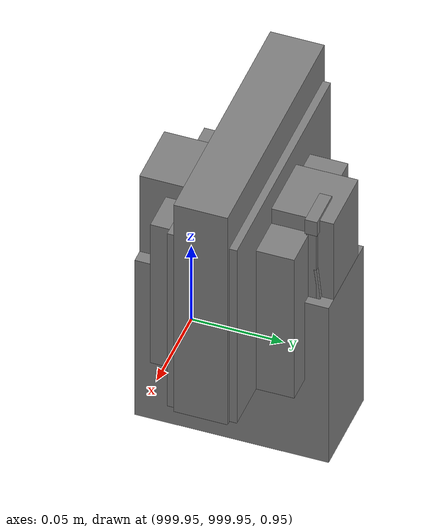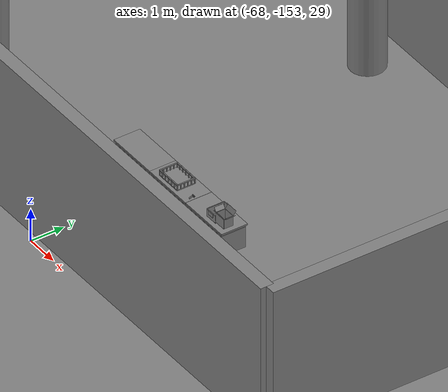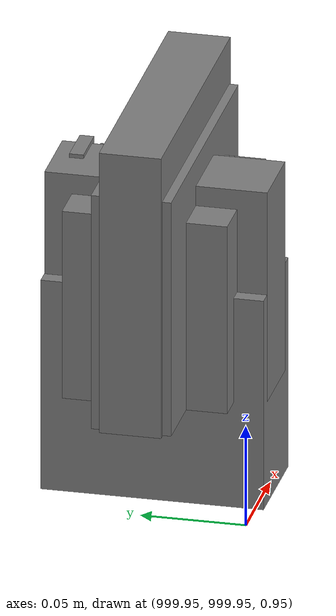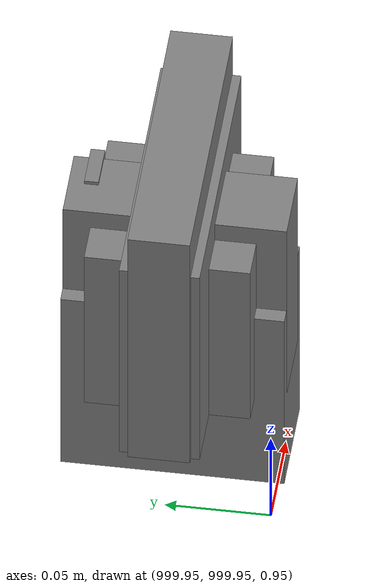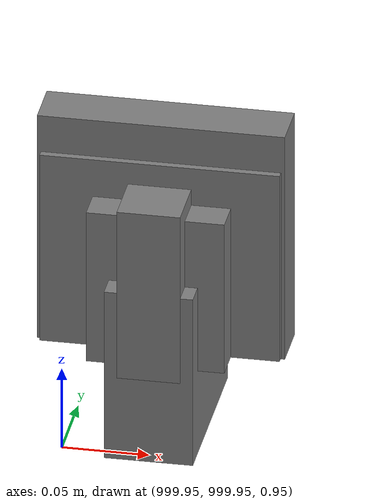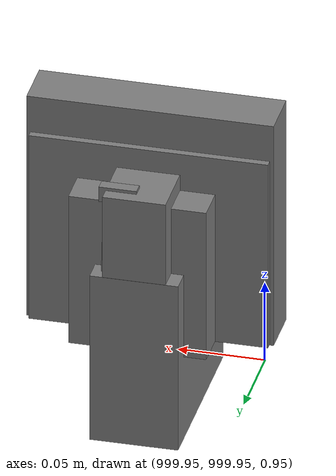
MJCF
<mujoco>
    <option gravity="0.000000000 0.000000000 -9.810000420" timestep="0.0049999999" integrator="implicitfast" density="1.225" viscosity="1.8000001e-05" noslip_iterations="10" iterations="100" sdf_iterations="50">
        <flag multiccd="disable"/>
    </option>
    <size memory="1000M"/>
    <compiler coordinate="local"/>
    <worldbody>
        <light cutoff="30" pos="0 1 1" dir="0 -1 -2"/>
        <light cutoff="30" pos="0 -1 1" dir="0 1 -2"/>
        <body pos="-64.866622925 -149.383972168 30.183746338" euler="89.999984741 89.999946594 0.000000000" name="openloong_gripper_2f85_fix_base_usda_bluebox_01">
            <geom contype="1" conaffinity="1" density="1000" type="box" material="" rgba="0.500000000 0.500000000 0.500000000 1.000000000" solimp="0.899999976 0.949999988 0.001000000" friction="1.000000000 0.005000000 0.000100000" solref="0.020000000 1.000000000" margin="0" condim="3" group="0" pos="0.276580811 0.187225342 0.000068665" quat="0.707106948 0.000077471 0.707106352 0.000077486" size="0.100000001 0.057999998 0.010000000" name="openloong_gripper_2f85_fix_base_usda_geom_BF397E16_BBA0_4512_B28F_29429DC6C387"/>
            <geom contype="1" conaffinity="1" density="1000" type="box" material="" rgba="0.500000000 0.500000000 0.500000000 1.000000000" solimp="0.899999976 0.949999988 0.001000000" friction="1.000000000 0.005000000 0.000100000" solref="0.020000000 1.000000000" margin="0" condim="3" group="0" pos="0.000000000 0.002883911 0.000000000" quat="0.999999881 0.000000000 0.000000000 0.000000000" size="0.254000008 0.003000000 0.172000006" name="openloong_gripper_2f85_fix_base_usda_geom_7A42AC59_E136_4668_BCFD_69CC2ABE6131"/>
            <geom contype="1" conaffinity="1" density="1000" type="box" material="" rgba="0.500000000 0.500000000 0.500000000 1.000000000" solimp="0.899999976 0.949999988 0.001000000" friction="1.000000000 0.005000000 0.000100000" solref="0.020000000 1.000000000" margin="0" condim="3" group="0" pos="0.000000000 0.124874115 0.173484802" quat="0.999796331 0.020176515 -0.000000015 0.000000030" size="0.259999990 0.119999997 0.007000000" name="openloong_gripper_2f85_fix_base_usda_geom_4F2E96FB_6F93_49D5_9012_01E3D9B3BE84"/>
            <geom contype="1" conaffinity="1" density="1000" type="box" material="" rgba="0.500000000 0.500000000 0.500000000 1.000000000" solimp="0.899999976 0.949999988 0.001000000" friction="1.000000000 0.005000000 0.000100000" solref="0.020000000 1.000000000" margin="0" condim="3" group="0" pos="0.000000000 0.124874115 -0.173469543" quat="0.999796331 -0.020176545 -0.000000015 0.000000000" size="0.259999990 0.119999997 0.007000000" name="openloong_gripper_2f85_fix_base_usda_geom_17789E6D_BC66_4405_AF2F_13EC94870EA0"/>
            <geom contype="1" conaffinity="1" density="1000" type="box" material="" rgba="0.500000000 0.500000000 0.500000000 1.000000000" solimp="0.899999976 0.949999988 0.001000000" friction="1.000000000 0.005000000 0.000100000" solref="0.020000000 1.000000000" margin="0" condim="3" group="0" pos="0.000000000 0.214008331 0.188980103" quat="0.999912977 0.013176724 0.000000015 0.000000000" size="0.259999990 0.029999999 0.012500000" name="openloong_gripper_2f85_fix_base_usda_geom_29295447_F4B6_44D5_85B9_62BC78E0B43D"/>
            <geom contype="1" conaffinity="1" density="1000" type="box" material="" rgba="0.500000000 0.500000000 0.500000000 1.000000000" solimp="0.899999976 0.949999988 0.001000000" friction="1.000000000 0.005000000 0.000100000" solref="0.020000000 1.000000000" margin="0" condim="3" group="0" pos="-0.258361816 0.125289917 0.001876831" quat="0.702796936 -0.020792112 0.710783124 0.020769298" size="0.189999998 0.119999997 0.009000000" name="openloong_gripper_2f85_fix_base_usda_geom_2B93DC1F_6FA8_4B32_9C2F_16FD54FA588E"/>
            <geom contype="1" conaffinity="1" density="1000" type="box" material="" rgba="0.500000000 0.500000000 0.500000000 1.000000000" solimp="0.899999976 0.949999988 0.001000000" friction="1.000000000 0.005000000 0.000100000" solref="0.020000000 1.000000000" margin="0" condim="3" group="0" pos="0.000000000 0.214008331 -0.188980103" quat="0.999912977 -0.013176769 0.000000030 0.000000015" size="0.259999990 0.029999999 0.012500000" name="openloong_gripper_2f85_fix_base_usda_geom_6C72EFE5_989D_411A_B797_0E8CA003F8BC"/>
            <geom contype="1" conaffinity="1" density="1000" type="box" material="" rgba="0.500000000 0.500000000 0.500000000 1.000000000" solimp="0.899999976 0.949999988 0.001000000" friction="1.000000000 0.005000000 0.000100000" solref="0.020000000 1.000000000" margin="0" condim="3" group="0" pos="-0.276611328 0.187225342 0.000068665" quat="0.707106650 0.000077441 0.707106709 0.000077456" size="0.100000001 0.057999998 0.010000000" name="openloong_gripper_2f85_fix_base_usda_geom_570280E8_3087_4BF8_824D_0963F3294C6F"/>
            <geom contype="1" conaffinity="1" density="1000" type="box" material="" rgba="0.500000000 0.500000000 0.500000000 1.000000000" solimp="0.899999976 0.949999988 0.001000000" friction="1.000000000 0.005000000 0.000100000" solref="0.020000000 1.000000000" margin="0" condim="3" group="0" pos="0.258331299 0.125289917 0.001876831" quat="0.702851415 0.018856421 0.710823774 -0.019329369" size="0.189999998 0.119999997 0.009000000" name="openloong_gripper_2f85_fix_base_usda_geom_1AD281E2_158B_45F1_B602_D43C84FB2FB9"/>
            <freejoint name="openloong_gripper_2f85_fix_base_usda_bluebox_01_joint"/>
            <site size="0.005000000 0.005000000 0.005000000" rgba="0.500000000 0.500000000 0.500000000 1.000000000" pos="0.000000000 0.000000000 0.000000000" quat="0.999961913 0.008726534 0.000000000 0.000000000" group="0" type="sphere" name="openloong_gripper_2f85_fix_base_usda_bluebox_01site"/>
        </body>
        <body pos="-64.496299744 -149.491867065 30.235729218" euler="0.000000000 0.000000000 89.999946594" name="openloong_gripper_2f85_fix_base_usda_cardboardbox_01">
            <geom contype="1" conaffinity="1" density="1000" type="box" material="" rgba="0.500000000 0.500000000 0.500000000 1.000000000" solimp="0.899999976 0.949999988 0.001000000" friction="1.000000000 0.005000000 0.000100000" solref="0.020000000 1.000000000" margin="0" condim="3" group="0" pos="-0.003166199 -0.004086494 0.005052090" quat="1.000000000 0.000000000 0.000000000 0.000000000" size="0.142499998 0.177500010 0.005000000" name="openloong_gripper_2f85_fix_base_usda_geom_21D29A15_2B4F_4ED6_AE75_F13F26B482A6"/>
            <geom contype="1" conaffinity="1" density="1000" type="box" material="" rgba="0.500000000 0.500000000 0.500000000 1.000000000" solimp="0.899999976 0.949999988 0.001000000" friction="1.000000000 0.005000000 0.000100000" solref="0.020000000 1.000000000" margin="0" condim="3" group="0" pos="-0.003166199 0.170316696 0.150570869" quat="1.000000000 0.000000000 0.000000000 0.000000000" size="0.142499998 0.005000000 0.149999991" name="openloong_gripper_2f85_fix_base_usda_geom_03A429BF_AEA3_41AC_92A3_F32BD323FC34"/>
            <geom contype="1" conaffinity="1" density="1000" type="box" material="" rgba="0.500000000 0.500000000 0.500000000 1.000000000" solimp="0.899999976 0.949999988 0.001000000" friction="1.000000000 0.005000000 0.000100000" solref="0.020000000 1.000000000" margin="0" condim="3" group="0" pos="-0.147399902 -0.005307198 0.150570869" quat="1.000000000 0.000000000 0.000000000 0.000000000" size="0.005000000 0.177500010 0.149999991" name="openloong_gripper_2f85_fix_base_usda_geom_9627DCF4_F3CC_4AB7_AA5E_2762F0897705"/>
            <geom contype="1" conaffinity="1" density="1000" type="box" material="" rgba="0.500000000 0.500000000 0.500000000 1.000000000" solimp="0.899999976 0.949999988 0.001000000" friction="1.000000000 0.005000000 0.000100000" solref="0.020000000 1.000000000" margin="0" condim="3" group="0" pos="0.140275955 -0.005307198 0.150570869" quat="1.000000000 0.000000000 0.000000000 0.000000000" size="0.005000000 0.177500010 0.149999991" name="openloong_gripper_2f85_fix_base_usda_geom_D44FE9C5_ED1B_48AA_A714_545E550BE4DF"/>
            <geom contype="1" conaffinity="1" density="1000" type="box" material="" rgba="0.500000000 0.500000000 0.500000000 1.000000000" solimp="0.899999976 0.949999988 0.001000000" friction="1.000000000 0.005000000 0.000100000" solref="0.020000000 1.000000000" margin="0" condim="3" group="0" pos="-0.003166199 -0.181550980 0.150570869" quat="1.000000000 0.000000000 0.000000000 0.000000000" size="0.142499998 0.005000000 0.149999991" name="openloong_gripper_2f85_fix_base_usda_geom_4F2438D1_BE35_4DC9_BF8A_E23AC6D666AF"/>
            <freejoint name="openloong_gripper_2f85_fix_base_usda_cardboardbox_01_joint"/>
            <site size="0.005000000 0.005000000 0.005000000" rgba="0.500000000 0.500000000 0.500000000 1.000000000" pos="0.000000000 0.000000000 0.000000000" quat="0.999961913 0.008726535 0.000000000 0.000000000" group="0" type="sphere" name="openloong_gripper_2f85_fix_base_usda_site_02888121_ADF2_4997_9292_EE011A259137"/>
            <body pos="0.139160156 -0.004048347 0.301930904" euler="-179.999954224 49.383502960 179.999954224" name="openloong_gripper_2f85_fix_base_usda_A1_006">
                <geom contype="1" conaffinity="1" density="1000" type="box" material="" rgba="0.500000000 0.500000000 0.500000000 1.000000000" solimp="0.899999976 0.949999988 0.001000000" friction="1.000000000 0.005000000 0.000100000" solref="0.020000000 1.000000000" margin="0" condim="3" group="0" pos="-0.071587563 0.000009537 0.001745224" quat="0.999999881 0.000000000 0.000000000 0.000000000" size="0.071249999 0.179999992 0.002500000" name="openloong_gripper_2f85_fix_base_usda_geom_E49C5789_19C1_4189_AAA7_50E92C4D3333"/>
                <joint armature="0" stiffness="0.07" damping="0.0099999998" axis="0.000000 1.000000 0.000000" type="hinge" name="openloong_gripper_2f85_fix_base_usda_A1_006"/>
            </body>
            <body pos="-0.145902634 -0.004086494 0.301938057" euler="-180.000000000 -60.000011444 -180.000000000" name="openloong_gripper_2f85_fix_base_usda_A2_006">
                <geom contype="1" conaffinity="1" density="1000" type="box" material="" rgba="0.500000000 0.500000000 0.500000000 1.000000000" solimp="0.899999976 0.949999988 0.001000000" friction="1.000000000 0.005000000 0.000100000" solref="0.020000000 1.000000000" margin="0" condim="3" group="0" pos="0.071268082 0.000009537 0.002717972" quat="0.000002921 0.000000000 -0.000000030 0.999999881" size="0.071249999 0.179999992 0.002500000" name="openloong_gripper_2f85_fix_base_usda_geom_016077DE_9482_49EA_8416_FFF09FFB1848"/>
                <joint armature="0" stiffness="0.07" damping="0.0099999998" axis="0.000000 1.000000 0.000000" type="hinge" name="openloong_gripper_2f85_fix_base_usda_A2_006"/>
            </body>
            <body pos="-0.003385544 0.175991058 0.301930904" euler="-125.858116150 -0.000004561 0.000002331" name="openloong_gripper_2f85_fix_base_usda_B2_006">
                <geom contype="1" conaffinity="1" density="1000" type="box" material="" rgba="0.500000000 0.500000000 0.500000000 1.000000000" solimp="0.899999976 0.949999988 0.001000000" friction="1.000000000 0.005000000 0.000100000" solref="0.020000000 1.000000000" margin="0" condim="3" group="0" pos="0.000009537 -0.070939064 -0.002470016" quat="0.999614120 0.027776197 -0.000000015 0.000000030" size="0.137500003 0.064999998 0.005000000" name="openloong_gripper_2f85_fix_base_usda_geom_0D182893_79EF_4B17_B46B_CB7009BF4123"/>
                <joint armature="0" stiffness="0.07" damping="0.0099999998" axis="1.000000 0.000000 0.000000" type="hinge" name="openloong_gripper_2f85_fix_base_usda_B2_006"/>
            </body>
            <body pos="-0.003385544 -0.184140205 0.301938057" euler="147.805557251 0.000000000 0.000000000" name="openloong_gripper_2f85_fix_base_usda_B1_006">
                <geom contype="1" conaffinity="1" density="1000" type="box" material="" rgba="0.500000000 0.500000000 0.500000000 1.000000000" solimp="0.899999976 0.949999988 0.001000000" friction="1.000000000 0.005000000 0.000100000" solref="0.020000000 1.000000000" margin="0" condim="3" group="0" pos="-0.000028610 0.070202351 -0.002703667" quat="0.999614179 -0.027776167 0.000000000 0.000000000" size="0.137500003 0.064999998 0.005000000" name="openloong_gripper_2f85_fix_base_usda_geom_16767413_1C95_47B8_B719_0ECE5B3A97D3"/>
                <joint armature="0" stiffness="0.07" damping="0.0099999998" axis="1.000000 0.000000 0.000000" type="hinge" name="openloong_gripper_2f85_fix_base_usda_B1_006"/>
            </body>
        </body>
        <body pos="-65.882858276 -149.481979370 30.229999542" euler="-64.487716675 0.000000000 0.000000000" name="openloong_gripper_2f85_fix_base_usda_Barcode">
            <geom contype="1" conaffinity="1" density="1000" type="box" material="" rgba="0.500000000 0.500000000 0.500000000 1.000000000" solimp="0.899999976 0.949999988 0.001000000" friction="1.000000000 0.005000000 0.000100000" solref="0.020000000 1.000000000" margin="0" condim="3" group="0" pos="0.000000000 0.013038635 0.001419067" quat="0.000000000 0.000000000 0.000000000 1.000000119" size="0.034000002 0.010000000 0.017999999" name="openloong_gripper_2f85_fix_base_usda_geom_96676C2C_AA2F_4CD8_BBB8_E45310185B2E"/>
            <geom contype="1" conaffinity="1" density="1000" type="box" material="" rgba="0.500000000 0.500000000 0.500000000 1.000000000" solimp="0.899999976 0.949999988 0.001000000" friction="1.000000000 0.005000000 0.000100000" solref="0.020000000 1.000000000" margin="0" condim="3" group="0" pos="0.000000000 -0.035301208 -0.007095337" quat="0.000000000 0.000000000 -0.043619365 0.999048233" size="0.028999999 0.010000000 0.020000000" name="openloong_gripper_2f85_fix_base_usda_geom_2B9B912D_4FB8_409E_80C1_8A163212DEDA"/>
            <geom contype="1" conaffinity="1" density="1000" type="box" material="" rgba="0.500000000 0.500000000 0.500000000 1.000000000" solimp="0.899999976 0.949999988 0.001000000" friction="1.000000000 0.005000000 0.000100000" solref="0.020000000 1.000000000" margin="0" condim="3" group="0" pos="0.000000000 -0.043411255 -0.011749268" quat="0.922262907 0.386563420 0.000000000 0.000000000" size="0.026000001 0.010000000 0.020000000" name="openloong_gripper_2f85_fix_base_usda_geom_9FF90E09_A872_401D_AA42_35FE556BBABA"/>
            <geom contype="1" conaffinity="1" density="1000" type="box" material="" rgba="0.500000000 0.500000000 0.500000000 1.000000000" solimp="0.899999976 0.949999988 0.001000000" friction="1.000000000 0.005000000 0.000100000" solref="0.020000000 1.000000000" margin="0" condim="3" group="0" pos="0.000000000 -0.016967773 -0.031860352" quat="0.000000000 0.000000000 0.000000000 1.000000119" size="0.008000000 0.010000000 0.013000000" name="openloong_gripper_2f85_fix_base_usda_geom_13CC4FFE_FD83_43A3_A46D_062B42D874FD"/>
            <geom contype="1" conaffinity="1" density="1000" type="box" material="" rgba="0.500000000 0.500000000 0.500000000 1.000000000" solimp="0.899999976 0.949999988 0.001000000" friction="1.000000000 0.005000000 0.000100000" solref="0.020000000 1.000000000" margin="0" condim="3" group="0" pos="0.000000000 -0.001869202 0.000312805" quat="0.953716993 0.300705761 0.000000000 0.000000000" size="0.032000002 0.010000000 0.018999999" name="openloong_gripper_2f85_fix_base_usda_geom_688CFF66_F225_41D7_89E9_FCFFCBA52366"/>
            <geom contype="1" conaffinity="1" density="1000" type="box" material="" rgba="0.500000000 0.500000000 0.500000000 1.000000000" solimp="0.899999976 0.949999988 0.001000000" friction="1.000000000 0.005000000 0.000100000" solref="0.020000000 1.000000000" margin="0" condim="3" group="0" pos="0.000000000 -0.019531250 -0.003173828" quat="0.953716993 0.300705761 0.000000000 0.000000000" size="0.030999999 0.010000000 0.020000000" name="openloong_gripper_2f85_fix_base_usda_geom_324BAB34_D0F8_403B_9FFD_4F1DBC678706"/>
            <geom contype="1" conaffinity="1" density="1000" type="box" material="" rgba="0.500000000 0.500000000 0.500000000 1.000000000" solimp="0.899999976 0.949999988 0.001000000" friction="1.000000000 0.005000000 0.000100000" solref="0.020000000 1.000000000" margin="0" condim="3" group="0" pos="0.000000000 -0.035301208 -0.007095337" quat="0.953716993 0.300705761 0.000000000 0.000000000" size="0.028999999 0.010000000 0.020000000" name="openloong_gripper_2f85_fix_base_usda_geom_4DC15708_8894_43A5_B331_8A42B2636795"/>
            <geom contype="1" conaffinity="1" density="1000" type="box" material="" rgba="0.500000000 0.500000000 0.500000000 1.000000000" solimp="0.899999976 0.949999988 0.001000000" friction="1.000000000 0.005000000 0.000100000" solref="0.020000000 1.000000000" margin="0" condim="3" group="0" pos="0.000000000 -0.042617798 -0.071121216" quat="0.000000000 0.000000000 0.000000000 1.000000119" size="0.013000000 0.021000000 0.059999999" name="openloong_gripper_2f85_fix_base_usda_geom_F4AD68F6_A6AC_43A6_9028_9482839B1EBF"/>
            <freejoint name="openloong_gripper_2f85_fix_base_usda_Barcode_joint"/>
            <site size="0.005000000 0.005000000 0.005000000" rgba="0.500000000 0.500000000 0.500000000 1.000000000" pos="0.000000000 0.000000000 0.000000000" quat="1.000000000 0.000000000 0.000000000 0.000000000" group="0" type="sphere" name="openloong_gripper_2f85_fix_base_usda_Barcode_site"/>
        </body>
        <body pos="-66.745018005 -149.392349243 30.184000015" euler="0.000000000 0.000000000 89.999946594" name="[22333531468142]_Basket_01">
            <geom contype="1" conaffinity="1" density="1000" type="box" material="" rgba="0.500000000 0.500000000 0.500000000 1.000000000" solimp="0.899999976 0.949999988 0.001000000" friction="1.000000000 0.005000000 0.000100000" solref="0.020000000 1.000000000" margin="0" condim="3" group="0" pos="-0.052425385 0.389207840 0.089787483" quat="0.707107008 0.000000000 0.000000000 0.707106411" size="0.014249999 0.014249999 0.059999999" name="[22333531468142]_geom_35614C0F_363D_4927_A7BF_CAB94B260F5D"/>
            <geom contype="1" conaffinity="1" density="1000" type="box" material="" rgba="0.500000000 0.500000000 0.500000000 1.000000000" solimp="0.899999976 0.949999988 0.001000000" friction="1.000000000 0.005000000 0.000100000" solref="0.020000000 1.000000000" margin="0" condim="3" group="0" pos="0.264015198 -0.133043289 0.089787483" quat="0.707107008 0.000000000 0.000000000 0.707106411" size="0.014249999 0.014249999 0.059999999" name="[22333531468142]_geom_CC7184AB_0843_47C8_A18E_D3F1E157226B"/>
            <geom contype="1" conaffinity="1" density="1000" type="box" material="" rgba="0.500000000 0.500000000 0.500000000 1.000000000" solimp="0.899999976 0.949999988 0.001000000" friction="1.000000000 0.005000000 0.000100000" solref="0.020000000 1.000000000" margin="0" condim="3" group="0" pos="-0.264015198 -0.265548706 0.089793205" quat="0.707107008 0.000000000 0.000000000 0.707106411" size="0.014249999 0.014249999 0.059999999" name="[22333531468142]_geom_07D01C79_E84D_412F_839B_4356E15A50BD"/>
            <geom contype="1" conaffinity="1" density="1000" type="box" material="" rgba="0.500000000 0.500000000 0.500000000 1.000000000" solimp="0.899999976 0.949999988 0.001000000" friction="1.000000000 0.005000000 0.000100000" solref="0.020000000 1.000000000" margin="0" condim="3" group="0" pos="-0.160263062 -0.389322281 0.089793205" quat="0.707107008 0.000000000 0.000000000 0.707106411" size="0.014249999 0.014249999 0.059999999" name="[22333531468142]_geom_307DA399_F55D_4EED_9599_FF26F3BDAC96"/>
            <geom contype="1" conaffinity="1" density="1000" type="box" material="" rgba="0.500000000 0.500000000 0.500000000 1.000000000" solimp="0.899999976 0.949999988 0.001000000" friction="1.000000000 0.005000000 0.000100000" solref="0.020000000 1.000000000" margin="0" condim="3" group="0" pos="0.162265778 -0.389322281 0.089787483" quat="0.707107008 0.000000000 0.000000000 0.707106411" size="0.014249999 0.014249999 0.059999999" name="[22333531468142]_geom_529910CE_7D6F_46B3_884C_DD2E6A8D5AB8"/>
            <geom contype="1" conaffinity="1" density="1000" type="box" material="" rgba="0.500000000 0.500000000 0.500000000 1.000000000" solimp="0.899999976 0.949999988 0.001000000" friction="1.000000000 0.005000000 0.000100000" solref="0.020000000 1.000000000" margin="0" condim="3" group="0" pos="0.264015198 0.389207840 0.089787483" quat="0.707107008 0.000000000 0.000000000 0.707106411" size="0.014249999 0.014249999 0.059999999" name="[22333531468142]_geom_45E82870_C674_4D3B_A67E_87FD6174BED3"/>
            <geom contype="1" conaffinity="1" density="1000" type="box" material="" rgba="0.500000000 0.500000000 0.500000000 1.000000000" solimp="0.899999976 0.949999988 0.001000000" friction="1.000000000 0.005000000 0.000100000" solref="0.020000000 1.000000000" margin="0" condim="3" group="0" pos="-0.264015198 -0.133043289 0.089793205" quat="0.707107008 0.000000000 0.000000000 0.707106411" size="0.014249999 0.014249999 0.059999999" name="[22333531468142]_geom_04A9100C_7EC4_4C9E_9FBD_E6C8C52D080C"/>
            <geom contype="1" conaffinity="1" density="1000" type="box" material="" rgba="0.500000000 0.500000000 0.500000000 1.000000000" solimp="0.899999976 0.949999988 0.001000000" friction="1.000000000 0.005000000 0.000100000" solref="0.020000000 1.000000000" margin="0" condim="3" group="0" pos="-0.264026642 0.269256592 0.089793205" quat="0.707107008 0.000000000 0.000000000 0.707106411" size="0.014249999 0.014249999 0.059999999" name="[22333531468142]_geom_7C395038_509B_4574_9064_3C221730A2FE"/>
            <geom contype="1" conaffinity="1" density="1000" type="box" material="" rgba="0.500000000 0.500000000 0.500000000 1.000000000" solimp="0.899999976 0.949999988 0.001000000" friction="1.000000000 0.005000000 0.000100000" solref="0.020000000 1.000000000" margin="0" condim="3" group="0" pos="0.054462433 0.389207840 0.089787483" quat="0.707107008 0.000000000 0.000000000 0.707106411" size="0.014249999 0.014249999 0.059999999" name="[22333531468142]_geom_62D63E13_0B03_43E9_BA97_50671C3D28E3"/>
            <geom contype="1" conaffinity="1" density="1000" type="box" material="" rgba="0.500000000 0.500000000 0.500000000 1.000000000" solimp="0.899999976 0.949999988 0.001000000" friction="1.000000000 0.005000000 0.000100000" solref="0.020000000 1.000000000" margin="0" condim="3" group="0" pos="0.054462433 -0.389322281 0.089787483" quat="0.707107008 0.000000000 0.000000000 0.707106411" size="0.014249999 0.014249999 0.059999999" name="[22333531468142]_geom_94B6B541_258D_4A85_B276_4086BA8BD2EC"/>
            <geom contype="1" conaffinity="1" density="1000" type="box" material="" rgba="0.500000000 0.500000000 0.500000000 1.000000000" solimp="0.899999976 0.949999988 0.001000000" friction="1.000000000 0.005000000 0.000100000" solref="0.020000000 1.000000000" margin="0" condim="3" group="0" pos="0.264015198 0.269256592 0.089793205" quat="0.707107008 0.000000000 0.000000000 0.707106411" size="0.014249999 0.014249999 0.059999999" name="[22333531468142]_geom_D3A81364_EF9F_4AF4_AAD5_D36B9C053BDC"/>
            <geom contype="1" conaffinity="1" density="1000" type="box" material="" rgba="0.500000000 0.500000000 0.500000000 1.000000000" solimp="0.899999976 0.949999988 0.001000000" friction="1.000000000 0.005000000 0.000100000" solref="0.020000000 1.000000000" margin="0" condim="3" group="0" pos="0.264015198 -0.389322281 0.089787483" quat="0.707107008 0.000000000 0.000000000 0.707106411" size="0.014249999 0.014249999 0.059999999" name="[22333531468142]_geom_8886D570_D359_4D79_A847_E7BF2CFE5B93"/>
            <geom contype="1" conaffinity="1" density="1000" type="box" material="" rgba="0.500000000 0.500000000 0.500000000 1.000000000" solimp="0.899999976 0.949999988 0.001000000" friction="1.000000000 0.005000000 0.000100000" solref="0.020000000 1.000000000" margin="0" condim="3" group="0" pos="0.000000000 0.000000000 0.015998840" quat="0.707107008 0.000000000 0.000000000 0.707106411" size="0.403499991 0.279000014 0.015750000" name="[22333531468142]_geom_C25DFF51_D2F0_4DD4_BBC5_9C8C07FAEED1"/>
            <geom contype="1" conaffinity="1" density="1000" type="box" material="" rgba="0.500000000 0.500000000 0.500000000 1.000000000" solimp="0.899999976 0.949999988 0.001000000" friction="1.000000000 0.005000000 0.000100000" solref="0.020000000 1.000000000" margin="0" condim="3" group="0" pos="0.000000000 -0.389476776 0.163619041" quat="0.707107008 0.000000000 0.000000000 0.707106411" size="0.015000000 0.277500004 0.015750000" name="[22333531468142]_geom_C7BD3E15_1640_4D14_B07D_F864BACB3733"/>
            <geom contype="1" conaffinity="1" density="1000" type="box" material="" rgba="0.500000000 0.500000000 0.500000000 1.000000000" solimp="0.899999976 0.949999988 0.001000000" friction="1.000000000 0.005000000 0.000100000" solref="0.020000000 1.000000000" margin="0" condim="3" group="0" pos="0.162265778 0.389207840 0.089787483" quat="0.707107008 0.000000000 0.000000000 0.707106411" size="0.014249999 0.014249999 0.059999999" name="[22333531468142]_geom_B9E9C3AC_5B03_46A8_8529_91C03F323E39"/>
            <geom contype="1" conaffinity="1" density="1000" type="box" material="" rgba="0.500000000 0.500000000 0.500000000 1.000000000" solimp="0.899999976 0.949999988 0.001000000" friction="1.000000000 0.005000000 0.000100000" solref="0.020000000 1.000000000" margin="0" condim="3" group="0" pos="0.000000000 0.389471054 0.163619041" quat="0.707107008 0.000000000 0.000000000 0.707106411" size="0.015000000 0.277500004 0.015750000" name="[22333531468142]_geom_BD655266_D354_483A_8D90_101FFB3A4F5D"/>
            <geom contype="1" conaffinity="1" density="1000" type="box" material="" rgba="0.500000000 0.500000000 0.500000000 1.000000000" solimp="0.899999976 0.949999988 0.001000000" friction="1.000000000 0.005000000 0.000100000" solref="0.020000000 1.000000000" margin="0" condim="3" group="0" pos="-0.263511658 0.000000000 0.163619041" quat="0.707107008 0.000000000 0.000000000 0.707106411" size="0.403499991 0.015000000 0.015750000" name="[22333531468142]_geom_6C02532E_6705_41CA_9D66_387DEFF30EDD"/>
            <geom contype="1" conaffinity="1" density="1000" type="box" material="" rgba="0.500000000 0.500000000 0.500000000 1.000000000" solimp="0.899999976 0.949999988 0.001000000" friction="1.000000000 0.005000000 0.000100000" solref="0.020000000 1.000000000" margin="0" condim="3" group="0" pos="-0.264015198 0.141334534 0.089793205" quat="0.707107008 0.000000000 0.000000000 0.707106411" size="0.014249999 0.014249999 0.059999999" name="[22333531468142]_geom_D3346490_04E9_4688_8A35_0427BCD9109F"/>
            <geom contype="1" conaffinity="1" density="1000" type="box" material="" rgba="0.500000000 0.500000000 0.500000000 1.000000000" solimp="0.899999976 0.949999988 0.001000000" friction="1.000000000 0.005000000 0.000100000" solref="0.020000000 1.000000000" margin="0" condim="3" group="0" pos="0.264015198 -0.265548706 0.089787483" quat="0.707107008 0.000000000 0.000000000 0.707106411" size="0.014249999 0.014249999 0.059999999" name="[22333531468142]_geom_594F740B_28C0_4405_AB1A_7590383CA57E"/>
            <geom contype="1" conaffinity="1" density="1000" type="box" material="" rgba="0.500000000 0.500000000 0.500000000 1.000000000" solimp="0.899999976 0.949999988 0.001000000" friction="1.000000000 0.005000000 0.000100000" solref="0.020000000 1.000000000" margin="0" condim="3" group="0" pos="-0.160263062 0.389207840 0.089787483" quat="0.707107008 0.000000000 0.000000000 0.707106411" size="0.014249999 0.014249999 0.059999999" name="[22333531468142]_geom_73EA0E8A_8901_423B_99B8_B0FCC8ADEFF6"/>
            <geom contype="1" conaffinity="1" density="1000" type="box" material="" rgba="0.500000000 0.500000000 0.500000000 1.000000000" solimp="0.899999976 0.949999988 0.001000000" friction="1.000000000 0.005000000 0.000100000" solref="0.020000000 1.000000000" margin="0" condim="3" group="0" pos="-0.052425385 -0.389322281 0.089787483" quat="0.707107008 0.000000000 0.000000000 0.707106411" size="0.014249999 0.014249999 0.059999999" name="[22333531468142]_geom_90290531_1FE4_44AC_BCDF_4B784E96489A"/>
            <geom contype="1" conaffinity="1" density="1000" type="box" material="" rgba="0.500000000 0.500000000 0.500000000 1.000000000" solimp="0.899999976 0.949999988 0.001000000" friction="1.000000000 0.005000000 0.000100000" solref="0.020000000 1.000000000" margin="0" condim="3" group="0" pos="-0.264026642 -0.389322281 0.089793205" quat="0.707107008 0.000000000 0.000000000 0.707106411" size="0.014249999 0.014249999 0.059999999" name="[22333531468142]_geom_14259DC2_CCAE_4626_A38D_158BB7169347"/>
            <geom contype="1" conaffinity="1" density="1000" type="box" material="" rgba="0.500000000 0.500000000 0.500000000 1.000000000" solimp="0.899999976 0.949999988 0.001000000" friction="1.000000000 0.005000000 0.000100000" solref="0.020000000 1.000000000" margin="0" condim="3" group="0" pos="0.264015198 0.141334534 0.089787483" quat="0.707107008 0.000000000 0.000000000 0.707106411" size="0.014249999 0.014249999 0.059999999" name="[22333531468142]_geom_F48911A5_93CB_4AB8_B11C_1BD937766469"/>
            <geom contype="1" conaffinity="1" density="1000" type="box" material="" rgba="0.500000000 0.500000000 0.500000000 1.000000000" solimp="0.899999976 0.949999988 0.001000000" friction="1.000000000 0.005000000 0.000100000" solref="0.020000000 1.000000000" margin="0" condim="3" group="0" pos="-0.264015198 0.389207840 0.089793205" quat="0.707107008 0.000000000 0.000000000 0.707106411" size="0.014249999 0.014249999 0.059999999" name="[22333531468142]_geom_5EF95202_46B3_4153_A9F7_6ADA00F7B8B1"/>
            <geom contype="1" conaffinity="1" density="1000" type="box" material="" rgba="0.500000000 0.500000000 0.500000000 1.000000000" solimp="0.899999976 0.949999988 0.001000000" friction="1.000000000 0.005000000 0.000100000" solref="0.020000000 1.000000000" margin="0" condim="3" group="0" pos="0.264015198 0.004480362 0.089787483" quat="0.707107008 0.000000000 0.000000000 0.707106411" size="0.014249999 0.014249999 0.059999999" name="[22333531468142]_geom_46B5337F_FE1A_4E21_8758_342E5D943BE3"/>
            <geom contype="1" conaffinity="1" density="1000" type="box" material="" rgba="0.500000000 0.500000000 0.500000000 1.000000000" solimp="0.899999976 0.949999988 0.001000000" friction="1.000000000 0.005000000 0.000100000" solref="0.020000000 1.000000000" margin="0" condim="3" group="0" pos="0.263694763 -0.000011444 0.163619041" quat="0.707107008 0.000000000 0.000000000 0.707106411" size="0.403499991 0.015000000 0.015750000" name="[22333531468142]_geom_CA88C926_6062_4FFE_ADA6_0A443800D5EA"/>
            <geom contype="1" conaffinity="1" density="1000" type="box" material="" rgba="0.500000000 0.500000000 0.500000000 1.000000000" solimp="0.899999976 0.949999988 0.001000000" friction="1.000000000 0.005000000 0.000100000" solref="0.020000000 1.000000000" margin="0" condim="3" group="0" pos="-0.264015198 0.004480362 0.089793205" quat="0.707107008 0.000000000 0.000000000 0.707106411" size="0.014249999 0.014249999 0.059999999" name="[22333531468142]_geom_029EA89E_4CBF_4E9D_A69F_23138D5075ED"/>
            <freejoint name="[22333531468142]_joint_9F445030_659F_4C0F_B292_8D6F0A09E7CB"/>
        </body>
        <body pos="0.000000000 0.000000000 0.000000000" euler="0.000000000 0.000000000 0.000000000" name="Static Objects_Static Objects">
            <geom contype="1" conaffinity="1" density="1000" type="box" material="" rgba="0.500000000 0.500000000 0.500000000 1.000000000" solimp="0.899999976 0.949999988 0.001000000" friction="1.000000000 0.005000000 0.000100000" solref="0.020000000 1.000000000" margin="0" condim="3" group="0" pos="-67.544113159 -149.365814209 29.727830887" quat="0.500000417 0.499999970 0.499999553 0.499999970" size="0.381000012 0.319999993 0.041000001" name="Static Objects_geom_1516F4CD_373A_4E30_B48F_64BF3BF2ECB7"/>
            <geom contype="1" conaffinity="1" density="1000" type="box" material="" rgba="0.500000000 0.500000000 0.500000000 1.000000000" solimp="0.899999976 0.949999988 0.001000000" friction="1.000000000 0.005000000 0.000100000" solref="0.020000000 1.000000000" margin="0" condim="3" group="0" pos="-68.239501953 -149.365814209 30.086868286" quat="0.500000417 0.499999970 0.499999553 0.499999970" size="0.370999992 0.039500002 0.745000005" name="Static Objects_geom_BE70AB92_CCEE_4DF7_8B81_05E173B21BE8"/>
            <geom contype="1" conaffinity="1" density="1000" type="box" material="" rgba="0.500000000 0.500000000 0.500000000 1.000000000" solimp="0.899999976 0.949999988 0.001000000" friction="1.000000000 0.005000000 0.000100000" solref="0.020000000 1.000000000" margin="0" condim="3" group="0" pos="-68.239501953 -149.365814209 30.147235870" quat="0.500000417 0.499999970 0.499999553 0.499999970" size="0.400000006 0.022000000 0.800000012" name="Static Objects_geom_9252C250_97BC_4F2A_B1B8_727A570A33CF"/>
            <geom contype="1" conaffinity="1" density="1000" type="box" material="" rgba="0.500000000 0.500000000 0.500000000 1.000000000" solimp="0.899999976 0.949999988 0.001000000" friction="1.000000000 0.005000000 0.000100000" solref="0.020000000 1.000000000" margin="0" condim="3" group="0" pos="-68.934890747 -149.365814209 29.727830887" quat="0.500000417 0.499999970 0.499999553 0.499999970" size="0.381000012 0.319999993 0.041000001" name="Static Objects_geom_041BBD75_6A92_496D_AE24_BBA90206CE99"/>
            <geom contype="1" conaffinity="1" density="1000" type="box" material="" rgba="0.500000000 0.500000000 0.500000000 1.000000000" solimp="0.899999976 0.949999988 0.001000000" friction="1.000000000 0.005000000 0.000100000" solref="0.020000000 1.000000000" margin="0" condim="3" group="0" pos="-68.239501953 -149.365814209 29.561563492" quat="0.500000417 0.499999970 0.499999553 0.499999970" size="0.020000000 0.022000000 0.660000026" name="Static Objects_geom_FA12FDFA_6CB6_4937_BF43_930B1AACF2BA"/>
            <geom contype="1" conaffinity="1" density="1000" type="box" material="" rgba="0.500000000 0.500000000 0.500000000 1.000000000" solimp="0.899999976 0.949999988 0.001000000" friction="1.000000000 0.005000000 0.000100000" solref="0.020000000 1.000000000" margin="0" condim="3" group="0" pos="-65.945671082 -149.365814209 29.727830887" quat="0.500000417 0.499999970 0.499999553 0.499999970" size="0.381000012 0.319999993 0.041000001" name="Static Objects_geom_B00B3081_A410_410F_BE46_B69A248C4C8B"/>
            <geom contype="1" conaffinity="1" density="1000" type="box" material="" rgba="0.500000000 0.500000000 0.500000000 1.000000000" solimp="0.899999976 0.949999988 0.001000000" friction="1.000000000 0.005000000 0.000100000" solref="0.020000000 1.000000000" margin="0" condim="3" group="0" pos="-66.641059875 -149.365814209 30.086868286" quat="0.500000417 0.499999970 0.499999553 0.499999970" size="0.370999992 0.039500002 0.745000005" name="Static Objects_geom_846C18D9_2F8C_4693_8045_716EEB0B3A1D"/>
            <geom contype="1" conaffinity="1" density="1000" type="box" material="" rgba="0.500000000 0.500000000 0.500000000 1.000000000" solimp="0.899999976 0.949999988 0.001000000" friction="1.000000000 0.005000000 0.000100000" solref="0.020000000 1.000000000" margin="0" condim="3" group="0" pos="-66.641059875 -149.365814209 30.147235870" quat="0.500000417 0.499999970 0.499999553 0.499999970" size="0.400000006 0.022000000 0.800000012" name="Static Objects_geom_99BDB12F_8B27_4C6E_9AED_473FD0236230"/>
            <geom contype="1" conaffinity="1" density="1000" type="box" material="" rgba="0.500000000 0.500000000 0.500000000 1.000000000" solimp="0.899999976 0.949999988 0.001000000" friction="1.000000000 0.005000000 0.000100000" solref="0.020000000 1.000000000" margin="0" condim="3" group="0" pos="-67.336448669 -149.365814209 29.727830887" quat="0.500000417 0.499999970 0.499999553 0.499999970" size="0.381000012 0.319999993 0.041000001" name="Static Objects_geom_DD412D07_EC8A_425A_887E_600BB3441929"/>
            <geom contype="1" conaffinity="1" density="1000" type="box" material="" rgba="0.500000000 0.500000000 0.500000000 1.000000000" solimp="0.899999976 0.949999988 0.001000000" friction="1.000000000 0.005000000 0.000100000" solref="0.020000000 1.000000000" margin="0" condim="3" group="0" pos="-66.641059875 -149.365814209 29.561563492" quat="0.500000417 0.499999970 0.499999553 0.499999970" size="0.020000000 0.022000000 0.660000026" name="Static Objects_geom_8FF1B05C_66CF_4514_8990_45C4B636E293"/>
            <geom contype="1" conaffinity="1" density="1000" type="box" material="" rgba="0.500000000 0.500000000 0.500000000 1.000000000" solimp="0.899999976 0.949999988 0.001000000" friction="1.000000000 0.005000000 0.000100000" solref="0.020000000 1.000000000" margin="0" condim="3" group="0" pos="-64.338577271 -149.365814209 29.727830887" quat="0.500000417 0.499999970 0.499999553 0.499999970" size="0.381000012 0.319999993 0.041000001" name="Static Objects_geom_1C8E4CC8_3F56_43B8_BD96_F49D12BC8AEF"/>
            <geom contype="1" conaffinity="1" density="1000" type="box" material="" rgba="0.500000000 0.500000000 0.500000000 1.000000000" solimp="0.899999976 0.949999988 0.001000000" friction="1.000000000 0.005000000 0.000100000" solref="0.020000000 1.000000000" margin="0" condim="3" group="0" pos="-65.033966064 -149.365814209 30.086868286" quat="0.500000417 0.499999970 0.499999553 0.499999970" size="0.370999992 0.039500002 0.745000005" name="Static Objects_geom_B0CFE35D_DB9A_4C3F_9966_5F782A3EF53C"/>
            <geom contype="1" conaffinity="1" density="1000" type="box" material="" rgba="0.500000000 0.500000000 0.500000000 1.000000000" solimp="0.899999976 0.949999988 0.001000000" friction="1.000000000 0.005000000 0.000100000" solref="0.020000000 1.000000000" margin="0" condim="3" group="0" pos="-65.033966064 -149.365814209 30.147235870" quat="0.500000417 0.499999970 0.499999553 0.499999970" size="0.400000006 0.022000000 0.800000012" name="Static Objects_geom_AC203DD1_3169_445B_B085_FFB04906765E"/>
            <geom contype="1" conaffinity="1" density="1000" type="box" material="" rgba="0.500000000 0.500000000 0.500000000 1.000000000" solimp="0.899999976 0.949999988 0.001000000" friction="1.000000000 0.005000000 0.000100000" solref="0.020000000 1.000000000" margin="0" condim="3" group="0" pos="-65.729354858 -149.365814209 29.727830887" quat="0.500000417 0.499999970 0.499999553 0.499999970" size="0.381000012 0.319999993 0.041000001" name="Static Objects_geom_8BC32AD5_08D3_42A7_A668_FD9443D664FA"/>
            <geom contype="1" conaffinity="1" density="1000" type="box" material="" rgba="0.500000000 0.500000000 0.500000000 1.000000000" solimp="0.899999976 0.949999988 0.001000000" friction="1.000000000 0.005000000 0.000100000" solref="0.020000000 1.000000000" margin="0" condim="3" group="0" pos="-65.033966064 -149.365814209 29.561563492" quat="0.500000417 0.499999970 0.499999553 0.499999970" size="0.020000000 0.022000000 0.660000026" name="Static Objects_geom_3EEEF493_076B_44FF_9E1E_AD04A06BD0E7"/>
            <geom contype="1" conaffinity="1" density="1000" type="box" material="" rgba="0.500000000 0.500000000 0.500000000 1.000000000" solimp="0.899999976 0.949999988 0.001000000" friction="1.000000000 0.005000000 0.000100000" solref="0.020000000 1.000000000" margin="0" condim="3" group="0" pos="-61.754566193 -137.853729248 33.906845093" quat="0.707107067 0.000000000 0.000000000 0.707106471" size="0.759999990 0.759999990 4.500000000" name="Static Objects_geom_5AA4E02D_A777_440D_BB3F_5BC5D54A76BD"/>
            <geom contype="1" conaffinity="1" density="1000" type="box" material="" rgba="0.500000000 0.500000000 0.500000000 1.000000000" solimp="0.899999976 0.949999988 0.001000000" friction="1.000000000 0.005000000 0.000100000" solref="0.020000000 1.000000000" margin="0" condim="3" group="0" pos="-57.511135101 -144.927108765 31.707921982" quat="1.000000000 0.000000000 0.000000000 0.000000000" size="0.200000003 8.000000000 2.299999952" name="Static Objects_geom_B211ED0F_7B64_4059_8133_1FD9794FF2EE"/>
            <geom contype="1" conaffinity="1" density="1000" type="box" material="" rgba="0.500000000 0.500000000 0.500000000 1.000000000" solimp="0.899999976 0.949999988 0.001000000" friction="1.000000000 0.005000000 0.000100000" solref="0.020000000 1.000000000" margin="0" condim="3" group="0" pos="-80.517646790 -157.574050903 31.688196182" quat="0.707107067 0.000000000 0.000000000 0.707106471" size="0.600000024 0.600000024 2.299999952" name="Static Objects_geom_870F80C5_50E2_4329_954B_EC1A07440BC3"/>
            <geom contype="1" conaffinity="1" density="1000" type="box" material="" rgba="0.500000000 0.500000000 0.500000000 1.000000000" solimp="0.899999976 0.949999988 0.001000000" friction="1.000000000 0.005000000 0.000100000" solref="0.020000000 1.000000000" margin="0" condim="3" group="0" pos="-80.711044312 -147.414932251 31.666158676" quat="1.000000000 0.000000000 0.000000000 0.000000000" size="0.200000003 10.000000000 2.299999952" name="Static Objects_geom_8BE7D750_5848_4098_8C29_DA9212615399"/>
            <geom contype="1" conaffinity="1" density="1000" type="box" material="" rgba="0.500000000 0.500000000 0.500000000 1.000000000" solimp="0.899999976 0.949999988 0.001000000" friction="1.000000000 0.005000000 0.000100000" solref="0.020000000 1.000000000" margin="0" condim="3" group="0" pos="-57.687217712 -137.434692383 31.688196182" quat="0.707107067 0.000000000 0.000000000 0.707106471" size="0.600000024 0.600000024 2.299999952" name="Static Objects_geom_ABF7FC19_16FB_4C24_ADFC_93A29C1123F0"/>
            <geom contype="1" conaffinity="1" density="1000" type="box" material="" rgba="0.500000000 0.500000000 0.500000000 1.000000000" solimp="0.899999976 0.949999988 0.001000000" friction="1.000000000 0.005000000 0.000100000" solref="0.020000000 1.000000000" margin="0" condim="3" group="0" pos="-69.537033081 -140.263229370 31.714921951" quat="0.707107067 0.000000000 0.000000000 0.707106471" size="0.759999990 4.500000000 2.299999952" name="Static Objects_geom_C0DB84AE_A96E_496B_8147_18A346F6D427"/>
            <geom contype="1" conaffinity="1" density="1000" type="box" material="" rgba="0.500000000 0.500000000 0.500000000 1.000000000" solimp="0.899999976 0.949999988 0.001000000" friction="1.000000000 0.005000000 0.000100000" solref="0.020000000 1.000000000" margin="0" condim="3" group="0" pos="-80.073638916 -137.853713989 33.906845093" quat="0.707107067 0.000000000 0.000000000 0.707106471" size="0.759999990 0.759999990 4.500000000" name="Static Objects_geom_EE8C8CE7_025F_4B9C_9FD0_7AF21CCA58B6"/>
            <geom contype="1" conaffinity="1" density="1000" type="box" material="" rgba="0.500000000 0.500000000 0.500000000 1.000000000" solimp="0.899999976 0.949999988 0.001000000" friction="1.000000000 0.005000000 0.000100000" solref="0.020000000 1.000000000" margin="0" condim="3" group="0" pos="-73.406707764 -155.734664917 31.707921982" quat="1.000000000 0.000000000 0.000000000 0.000000000" size="0.200000003 3.000000000 2.299999952" name="Static Objects_geom_9FB95FFA_D98F_4EB7_BB8E_6611298A8678"/>
            <geom contype="1" conaffinity="1" density="1000" type="box" material="" rgba="0.500000000 0.500000000 0.500000000 1.000000000" solimp="0.899999976 0.949999988 0.001000000" friction="1.000000000 0.005000000 0.000100000" solref="0.020000000 1.000000000" margin="0" condim="3" group="0" pos="-68.497543335 -137.448257446 31.707921982" quat="0.707107067 0.000000000 0.000000000 0.707106471" size="0.200000003 14.000000000 2.299999952" name="Static Objects_geom_97B89047_019E_4C95_83FF_86A4CD8DA12F"/>
            <geom contype="1" conaffinity="1" density="1000" type="cylinder" material="" rgba="0.500000000 0.500000000 0.500000000 1.000000000" solimp="0.899999976 0.949999988 0.001000000" friction="1.000000000 0.005000000 0.000100000" solref="0.020000000 1.000000000" margin="0" condim="3" group="0" pos="-68.868522644 -142.134506226 31.711090088" quat="0.707107067 0.000000000 0.000000000 0.707106471" size="0.509999990 2.299999952 1.000000000" name="Static Objects_geom_CE3CD3FF_07F3_4403_98C7_3A13117B9EB8"/>
            <geom contype="1" conaffinity="1" density="1000" type="plane" material="" rgba="0.500000000 0.500000000 0.500000000 1.000000000" solimp="0.899999976 0.949999988 0.001000000" friction="1.000000000 0.005000000 0.000100000" solref="0.020000000 1.000000000" margin="0" condim="3" group="0" pos="-72.873703003 -147.131927490 29.409669876" quat="1.000000000 0.000000000 0.000000000 0.000000000" size="18.000000000 14.000000000 1.000000000" name="Static Objects_geom_B57DFE8D_A71D_4524_8AED_296B8A6B4058"/>
            <geom contype="1" conaffinity="1" density="1000" type="box" material="" rgba="0.500000000 0.500000000 0.500000000 1.000000000" solimp="0.899999976 0.949999988 0.001000000" friction="1.000000000 0.005000000 0.000100000" solref="0.020000000 1.000000000" margin="0" condim="3" group="0" pos="-79.943580627 -157.782272339 31.707921982" quat="0.707107067 0.000000000 0.000000000 0.707106471" size="0.200000003 7.000000000 2.299999952" name="Static Objects_geom_99ACA2AD_494D_42C2_A1EA_7226E2C1576A"/>
            <geom contype="1" conaffinity="1" density="1000" type="box" material="" rgba="0.500000000 0.500000000 0.500000000 1.000000000" solimp="0.899999976 0.949999988 0.001000000" friction="1.000000000 0.005000000 0.000100000" solref="0.020000000 1.000000000" margin="0" condim="3" group="0" pos="-65.421028137 -152.903442383 31.707921982" quat="0.707107067 0.000000000 0.000000000 0.707106471" size="0.200000003 7.800000191 2.299999952" name="Static Objects_geom_C9C6FEAD_209C_46FC_895A_8E7BDD3EAC8B"/>
            <geom contype="1" conaffinity="1" density="1000" type="box" material="" rgba="0.500000000 0.500000000 0.500000000 1.000000000" solimp="0.899999976 0.949999988 0.001000000" friction="1.000000000 0.005000000 0.000100000" solref="0.020000000 1.000000000" margin="0" condim="3" group="0" pos="-74.776908875 -149.964416504 31.688196182" quat="1.000000000 0.000000000 0.000000000 0.000000000" size="0.600000024 0.409999996 2.299999952" name="Static Objects_geom_8547DE75_358B_4537_B668_D7DA27A7363F"/>
            <geom contype="1" conaffinity="1" density="1000" type="cylinder" material="" rgba="0.500000000 0.500000000 0.500000000 1.000000000" solimp="0.899999976 0.949999988 0.001000000" friction="1.000000000 0.005000000 0.000100000" solref="0.020000000 1.000000000" margin="0" condim="3" group="0" pos="-60.161884308 -142.134506226 31.711090088" quat="0.707107067 0.000000000 0.000000000 0.707106471" size="0.509999990 2.299999952 1.000000000" name="Static Objects_geom_2D35B88D_21E1_433F_8E55_489D2C19BE8D"/>
            <geom contype="1" conaffinity="1" density="1000" type="cylinder" material="" rgba="0.500000000 0.500000000 0.500000000 1.000000000" solimp="0.899999976 0.949999988 0.001000000" friction="1.000000000 0.005000000 0.000100000" solref="0.020000000 1.000000000" margin="0" condim="3" group="0" pos="-75.382453918 -149.963455200 31.711090088" quat="0.707107067 0.000000000 0.000000000 0.707106471" size="0.409999996 2.299999952 1.000000000" name="Static Objects_geom_D7521A0F_ED4F_4FA5_B06A_0DA47CBE7E08"/>
            <geom contype="1" conaffinity="1" density="1000" type="cylinder" material="" rgba="0.500000000 0.500000000 0.500000000 1.000000000" solimp="0.899999976 0.949999988 0.001000000" friction="1.000000000 0.005000000 0.000100000" solref="0.020000000 1.000000000" margin="0" condim="3" group="0" pos="-74.154960632 -149.963455200 31.711090088" quat="0.707107067 0.000000000 0.000000000 0.707106471" size="0.409999996 2.299999952 1.000000000" name="Static Objects_geom_BEEF9048_E210_4586_97D4_F481DFADECFF"/>
            <geom contype="1" conaffinity="1" density="1000" type="cylinder" material="" rgba="0.500000000 0.500000000 0.500000000 1.000000000" solimp="0.899999976 0.949999988 0.001000000" friction="1.000000000 0.005000000 0.000100000" solref="0.020000000 1.000000000" margin="0" condim="3" group="0" pos="-77.566612244 -142.134506226 31.711090088" quat="0.707107067 0.000000000 0.000000000 0.707106471" size="0.509999990 2.299999952 1.000000000" name="Static Objects_geom_D63546DA_FB18_4919_AFFC_F9FD71D95A04"/>
        </body>
        <body pos="-66.193641663 -149.736877441 31.163057327" euler="-55.312713623 -78.884834290 -112.394035339" mocap="true" name="spotlight4_SpotLight"/>
        <body pos="1000.000000000 1000.000000000 1.000000000" euler="0.000000000 0.000000000 180.000000000" name="openloong_gripper_2f85_fix_base_usda_battery_01">
            <geom contype="1" conaffinity="1" density="1000" type="box" material="" rgba="0.500000000 0.500000000 0.500000000 1.000000000" solimp="0.899999976 0.949999988 0.001000000" friction="1.000000000 0.005000000 0.000100000" solref="0.020000000 1.000000000" margin="0" condim="3" group="0" pos="-0.011123657 -0.041940309 0.101691343" quat="1.000000000 0.000000000 0.000000000 0.000000000" size="0.010800000 0.003375000 0.004725000" name="openloong_gripper_2f85_fix_base_usda_geom_80AF4AB0_6082_44A9_9AC6_7789AA069FC5"/>
            <geom contype="1" conaffinity="1" density="1000" type="box" material="" rgba="0.500000000 0.500000000 0.500000000 1.000000000" solimp="0.899999976 0.949999988 0.001000000" friction="1.000000000 0.005000000 0.000100000" solref="0.020000000 1.000000000" margin="0" condim="3" group="0" pos="-0.010876465 -0.044247437 0.047066893" quat="0.998702705 -0.050920475 0.000000000 0.000000000" size="0.009450001 0.002700000 0.024975000" name="openloong_gripper_2f85_fix_base_usda_geom_98DBBEEA_DD02_461A_B9BB_40D4097F9840"/>
            <geom contype="1" conaffinity="1" density="1000" type="box" material="" rgba="0.500000000 0.500000000 0.500000000 1.000000000" solimp="0.899999976 0.949999988 0.001000000" friction="1.000000000 0.005000000 0.000100000" solref="0.020000000 1.000000000" margin="0" condim="3" group="0" pos="-0.001235962 -0.000659180 0.047381196" quat="1.000000000 0.000000000 0.000000000 0.000000000" size="0.039420001 0.039150000 0.047250003" name="openloong_gripper_2f85_fix_base_usda_geom_12FBA74A_80B6_44B5_A324_2424E4569985"/>
            <geom contype="1" conaffinity="1" density="1000" type="box" material="" rgba="0.500000000 0.500000000 0.500000000 1.000000000" solimp="0.899999976 0.949999988 0.001000000" friction="1.000000000 0.005000000 0.000100000" solref="0.020000000 1.000000000" margin="0" condim="3" group="0" pos="-0.010876465 -0.039138794 0.009851727" quat="1.000000000 0.000000000 0.000000000 0.000000000" size="0.009450001 0.010800000 0.013500000" name="openloong_gripper_2f85_fix_base_usda_geom_9F4C1243_FABF_4FEE_9A7D_403797AFB7FE"/>
            <geom contype="1" conaffinity="1" density="1000" type="box" material="" rgba="0.500000000 0.500000000 0.500000000 1.000000000" solimp="0.899999976 0.949999988 0.001000000" friction="1.000000000 0.005000000 0.000100000" solref="0.020000000 1.000000000" margin="0" condim="3" group="0" pos="-0.010876465 -0.041528322 0.071508206" quat="1.000000000 0.000000000 0.000000000 0.000000000" size="0.009450001 0.002700000 0.027000001" name="openloong_gripper_2f85_fix_base_usda_geom_A6F9D14C_9E1C_4701_ACE7_4B59E67A2D1D"/>
            <freejoint name="openloong_gripper_2f85_fix_base_usda_battery_01_joint"/>
            <site size="0.005000000 0.005000000 0.005000000" rgba="0.500000000 0.500000000 0.500000000 1.000000000" pos="0.000000000 0.000000000 0.000000000" quat="0.999961913 0.008726500 0.000000000 0.000000000" group="0" type="sphere" name="openloong_gripper_2f85_fix_base_usda_battery_01site"/>
        </body>
        <body pos="1000.000000000 1000.000000000 1.000000000" euler="0.000000000 0.000000000 180.000000000" name="openloong_gripper_2f85_fix_base_usda_cpu_fan">
            <geom contype="1" conaffinity="1" density="1000" type="box" material="" rgba="0.500000000 0.500000000 0.500000000 1.000000000" solimp="0.899999976 0.949999988 0.001000000" friction="1.000000000 0.005000000 0.000100000" solref="0.020000000 1.000000000" margin="0" condim="3" group="0" pos="0.000000000 0.000000000 0.070034981" quat="0.000000000 0.000000000 0.000000000 1.000000000" size="0.070700005 0.014699999 0.070700005" name="openloong_gripper_2f85_fix_base_usda_geom_576587CF_11BD_4F52_A933_912F235078A5"/>
            <freejoint name="openloong_gripper_2f85_fix_base_usda_cpu_fan_joint"/>
            <site size="0.005000000 0.005000000 0.005000000" rgba="0.500000000 0.500000000 0.500000000 1.000000000" pos="0.000000000 0.000000000 0.000000000" quat="0.999961913 0.008726535 0.000000000 0.000000000" group="0" type="sphere" name="openloong_gripper_2f85_fix_base_usda_cpu_fancsite"/>
        </body>
        <body pos="1000.000000000 1000.000000000 1.000000000" euler="0.000000000 0.000000000 180.000000000" name="openloong_gripper_2f85_fix_base_usda_wifi_box">
            <geom contype="1" conaffinity="1" density="1000" type="box" material="" rgba="0.500000000 0.500000000 0.500000000 1.000000000" solimp="0.899999976 0.949999988 0.001000000" friction="1.000000000 0.005000000 0.000100000" solref="0.020000000 1.000000000" margin="0" condim="3" group="0" pos="0.000000000 0.000000000 0.058978677" quat="0.000000000 0.000000047 0.000000000 1.000000000" size="0.068499997 0.018999999 0.059000000" name="openloong_gripper_2f85_fix_base_usda_geom_0FBCDA9B_43C6_4EA0_80A2_95538DC6D699"/>
            <freejoint name="openloong_gripper_2f85_fix_base_usda_wifi_box_joint"/>
            <site size="0.005000000 0.005000000 0.005000000" rgba="0.500000000 0.500000000 0.500000000 1.000000000" pos="0.000000000 0.000000000 0.000000000" quat="0.999961913 0.008726500 0.000000000 0.000000000" group="0" type="sphere" name="openloong_gripper_2f85_fix_base_usda_wifi_boxsite"/>
        </body>
        <body pos="-66.231117249 -149.099090576 31.170482635" euler="-2.724478722 84.268333435 -110.811935425" mocap="true" name="spotlight6_SpotLight"/>
        <body pos="1000.000000000 1000.000000000 1.000000000" euler="0.000011953 0.000005123 -179.999984741" name="openloong_gripper_2f85_fix_base_usda_intel_box">
            <geom contype="1" conaffinity="1" density="1000" type="box" material="" rgba="0.500000000 0.500000000 0.500000000 1.000000000" solimp="0.899999976 0.949999988 0.001000000" friction="1.000000000 0.005000000 0.000100000" solref="0.020000000 1.000000000" margin="0" condim="3" group="0" pos="0.000000000 -0.000067139 0.000082284" quat="0.707106709 0.000000225 0.000000253 0.707106650" size="0.052800003 0.025300000 0.052800003" name="openloong_gripper_2f85_fix_base_usda_geom_536AA3B6_362B_460A_A7CB_CB4D2E1C387F"/>
            <freejoint name="openloong_gripper_2f85_fix_base_usda_intel_box_joint"/>
            <site size="0.005000000 0.005000000 0.005000000" rgba="0.500000000 0.500000000 0.500000000 1.000000000" pos="0.000000000 0.000000000 0.000000000" quat="0.999961913 0.008726500 0.000000000 0.000000000" group="0" type="sphere" name="openloong_gripper_2f85_fix_base_usda_intel_boxsite"/>
        </body>
        <body pos="1000.000000000 999.999938965 1.000000000" euler="0.000000000 0.000000000 180.000000000" name="openloong_gripper_2f85_fix_base_usda_intelcore_i5">
            <geom contype="1" conaffinity="1" density="1000" type="box" material="" rgba="0.500000000 0.500000000 0.500000000 1.000000000" solimp="0.899999976 0.949999988 0.001000000" friction="1.000000000 0.005000000 0.000100000" solref="0.020000000 1.000000000" margin="0" condim="3" group="0" pos="0.000000000 0.000000000 0.051722717" quat="0.707106709 0.000000000 0.000000000 -0.707106769" size="0.052800000 0.018080002 0.052800000" name="openloong_gripper_2f85_fix_base_usda_geom_30C83237_01D8_4D30_B223_6C65DC506569"/>
            <freejoint name="openloong_gripper_2f85_fix_base_usda_intelcore_i5_joint"/>
            <site size="0.005000000 0.005000000 0.005000000" rgba="0.500000000 0.500000000 0.500000000 1.000000000" pos="0.000000000 0.000000000 0.000000000" quat="0.999961913 0.008726534 0.000000000 0.000000000" group="0" type="sphere" name="openloong_gripper_2f85_fix_base_usda_intelcore_i5site"/>
        </body>
        <body pos="-66.046936035 -149.350906372 31.165267944" euler="81.308738708 -54.743507385 73.981842041" mocap="true" name="spotlight1_SpotLight"/>
        <body pos="-66.291030884 -149.869689941 29.018842697" euler="0.000000000 0.000000000 89.999946594" mocap="true" name="openloong_gripper_2f85_fix_base_usda_leftHandMocap"/>
        <body pos="-66.291030884 -149.869689941 29.018842697" euler="0.000000000 0.000000000 89.999946594" mocap="true" name="openloong_gripper_2f85_fix_base_usda_rightHandMocap"/>
        <body pos="-66.291030884 -149.869689941 30.218843460" euler="0.000000000 0.000000000 89.999946594" name="openloong_gripper_2f85_fix_base_usda_base_link">
            <geom contype="1" conaffinity="1" density="1000" type="mesh" material="" rgba="0.783999979 0.783999979 0.783999979 1.000000000" solimp="0.899999976 0.949999988 0.001000000" friction="1.000000000 0.005000000 0.000100000" solref="0.020000000 1.000000000" margin="0" condim="3" group="3" mesh="base_link" pos="0.000000000 0.000000000 0.000000000" quat="1.000000000 0.000000000 0.000000000 0.000000000" size="1.000000000 1.000000000 1.000000000" name="openloong_gripper_2f85_fix_base_usda__geom_7_CC126456_7721_46DF_92AB_3FA37E988415"/>
            <site size="0.005000000 0.005000000 0.005000000" rgba="0.500000000 0.500000000 0.500000000 1.000000000" pos="0.000000000 0.000000000 0.000000000" quat="1.000000000 0.000000000 0.000000000 0.000000000" group="0" type="sphere" name="openloong_gripper_2f85_fix_base_usda_imu"/>
            <inertial mass="22.447001" pos="-0.005664100 -0.001336700 0.238289997" diaginertia="0.374352545 0.277180195 0.220617250" quat="0.999247074 0.035235517 -0.015086859 0.006023135"/>
            <body pos="0.000000000 0.000000000 0.299997330" euler="0.000000000 0.000000000 0.000000000" name="openloong_gripper_2f85_fix_base_usda_dummy_body">
                <geom contype="1" conaffinity="1" density="1000" type="sphere" material="" rgba="0.783999979 0.783999979 0.783999979 1.000000000" solimp="0.899999976 0.949999988 0.001000000" friction="1.000000000 0.005000000 0.000100000" solref="0.020000000 1.000000000" margin="0" condim="3" group="3" pos="0.000000000 0.000000000 0.000000000" quat="1.000000000 0.000000000 0.000000000 0.000000000" size="0.010000000 0.000000000 0.000000000" name="openloong_gripper_2f85_fix_base_usda__geom_8_827398BC_EC86_42CF_BE25_20FAB1951359"/>
                <joint armature="0.0099999998" stiffness="0" damping="0.1" axis="0.000000 0.000000 1.000000" type="hinge" name="openloong_gripper_2f85_fix_base_usda_dummy_joint"/>
                <site size="0.010000000 0.005000000 0.005000000" rgba="0.500000000 0.500000000 0.500000000 1.000000000" pos="0.000000000 0.000000000 0.000000000" quat="1.000000000 0.000000000 0.000000000 0.000000000" group="3" type="sphere" name="openloong_gripper_2f85_fix_base_usda_dummy_site"/>
            </body>
            <body pos="0.009002686 0.000000000 0.406400681" euler="0.000000000 0.000000000 0.000000000" name="openloong_gripper_2f85_fix_base_usda_Link_head_yaw">
                <geom contype="1" conaffinity="1" density="1000" type="mesh" material="" rgba="0.783999979 0.783999979 0.783999979 1.000000000" solimp="0.899999976 0.949999988 0.001000000" friction="1.000000000 0.005000000 0.000100000" solref="0.020000000 1.000000000" margin="0" condim="3" group="3" mesh="Link_head_yaw" pos="0.000000000 0.000000000 0.000000000" quat="1.000000000 0.000000000 0.000000000 0.000000000" size="1.000000000 1.000000000 1.000000000" name="openloong_gripper_2f85_fix_base_usda__geom_10_4A3AEBEE_1155_4061_B216_82D5E5D243A9"/>
                <inertial mass="0.84249002" pos="0.000000000 -0.002081400 0.044801001" diaginertia="0.000700588 0.000629000 0.000553812" quat="0.706933022 -0.015675601 0.015677100 0.706933022"/>
                <body pos="0.000000000 -0.034599304 0.048500061" euler="0.000000000 0.000000000 0.000000000" name="openloong_gripper_2f85_fix_base_usda_Link_head_pitch">
                    <geom contype="1" conaffinity="1" density="1000" type="mesh" material="" rgba="0.783999979 0.783999979 0.783999979 1.000000000" solimp="0.899999976 0.949999988 0.001000000" friction="1.000000000 0.005000000 0.000100000" solref="0.020000000 1.000000000" margin="0" condim="3" group="3" mesh="Link_head_pitch" pos="0.000000000 0.000000000 0.000000000" quat="1.000000000 0.000000000 0.000000000 0.000000000" size="1.000000000 1.000000000 1.000000000" name="openloong_gripper_2f85_fix_base_usda__geom_12_1C3BEC8A_5DB5_45BF_B174_7B7CA776AD71"/>
                    <inertial mass="1.3943" pos="0.020569000 0.033004001 0.125000000" diaginertia="0.006381400 0.006289940 0.004481460" quat="0.973390222 0.008406822 0.228157058 0.019624906"/>
                    <body pos="0.000000000 0.029998779 0.000000000" euler="0.000000000 0.000000000 0.000000000" name="openloong_gripper_2f85_fix_base_usda_neck_center_body">
                        <site size="0.010000000 0.005000000 0.005000000" rgba="0.500000000 0.500000000 0.500000000 1.000000000" pos="0.000000000 0.000000000 0.000000000" quat="1.000000000 0.000000000 0.000000000 0.000000000" group="3" type="sphere" name="openloong_gripper_2f85_fix_base_usda_neck_center_site"/>
                        <body pos="0.020004272 0.000000000 0.149999619" euler="-0.000002229 39.998176575 -90.000205994" name="openloong_gripper_2f85_fix_base_usda_camera_head">
                            <site size="0.010000000 0.005000000 0.005000000" rgba="0.500000000 0.500000000 0.500000000 1.000000000" pos="0.000000000 0.000000000 0.000000000" quat="1.000000000 0.000000000 0.000000000 0.000000000" group="3" type="sphere" name="openloong_gripper_2f85_fix_base_usda_camera_head_site"/>
                        </body>
                    </body>
                </body>
            </body>
            <body pos="0.003997803 -0.161598206 0.392200470" euler="0.000000000 0.000000000 0.000000000" name="openloong_gripper_2f85_fix_base_usda_Link_arm_r_01">
                <geom contype="1" conaffinity="1" density="1000" type="mesh" material="" rgba="0.783999979 0.783999979 0.783999979 1.000000000" solimp="0.899999976 0.949999988 0.001000000" friction="1.000000000 0.005000000 0.000100000" solref="0.020000000 1.000000000" margin="0" condim="3" group="3" mesh="Link_arm_r_01" pos="0.000000000 0.000000000 0.000000000" quat="1.000000000 0.000000000 0.000000000 0.000000000" size="1.000000000 1.000000000 1.000000000" name="openloong_gripper_2f85_fix_base_usda__geom_14_C671081F_02FD_42AE_8878_B763FD967D7B"/>
                <joint armature="0.0099999998" stiffness="0" damping="1" axis="0.000000 -1.000000 0.000000" limited="true" range="-170.000015259 170.000015259" type="hinge" name="openloong_gripper_2f85_fix_base_usda_J_arm_r_01"/>
                <inertial mass="0.75641" pos="0.004494600 -0.038293999 -0.000001874" diaginertia="0.000842990 0.000803050 0.000587120" quat="-0.000163502 0.707098067 0.000812463 0.707115054"/>
                <body pos="-0.041992188 -0.041000366 0.000000000" euler="0.000000000 0.000000000 0.000000000" name="openloong_gripper_2f85_fix_base_usda_Link_arm_r_02">
                    <geom contype="1" conaffinity="1" density="1000" type="mesh" material="" rgba="0.783999979 0.783999979 0.783999979 1.000000000" solimp="0.899999976 0.949999988 0.001000000" friction="1.000000000 0.005000000 0.000100000" solref="0.020000000 1.000000000" margin="0" condim="3" group="3" mesh="Link_arm_r_02" pos="0.000000000 0.000000000 0.000000000" quat="1.000000000 0.000000000 0.000000000 0.000000000" size="1.000000000 1.000000000 1.000000000" name="openloong_gripper_2f85_fix_base_usda__geom_16_53714DEE_2367_41E4_B430_E49AFF18C184"/>
                    <joint armature="0.0099999998" stiffness="0" damping="1" axis="-1.000000 0.000000 0.000000" limited="true" range="-105.000244141 105.000244141" type="hinge" name="openloong_gripper_2f85_fix_base_usda_J_arm_r_02"/>
                    <inertial mass="0.98500001" pos="0.041999999 -0.067430697 0.000000000" diaginertia="0.002262690 0.001730990 0.001154020" quat="0.500000000 0.500000000 -0.500000000 0.500000000"/>
                    <body pos="0.041992188 -0.122596741 0.000000000" euler="0.000000000 0.000000000 0.000000000" name="openloong_gripper_2f85_fix_base_usda_Link_arm_r_03">
                        <geom contype="1" conaffinity="1" density="1000" type="mesh" material="" rgba="0.783999979 0.783999979 0.783999979 1.000000000" solimp="0.899999976 0.949999988 0.001000000" friction="1.000000000 0.005000000 0.000100000" solref="0.020000000 1.000000000" margin="0" condim="3" group="3" mesh="Link_arm_r_03" pos="0.000000000 0.000000000 0.000000000" quat="1.000000000 0.000000000 0.000000000 0.000000000" size="1.000000000 1.000000000 1.000000000" name="openloong_gripper_2f85_fix_base_usda__geom_18_D8D09B00_434D_4E3A_81EA_1C8C5B97628D"/>
                        <joint armature="0.0099999998" stiffness="0" damping="1" axis="0.000000 -1.000000 0.000000" limited="true" range="-170.000015259 170.000015259" type="hinge" name="openloong_gripper_2f85_fix_base_usda_J_arm_r_03"/>
                        <inertial mass="0.95899999" pos="-0.001413580 -0.164663002 0.020757901" diaginertia="0.002101340 0.002064590 0.000754802" quat="0.560480952 0.454391927 -0.443732947 0.531497955"/>
                        <body pos="0.035293579 -0.177406311 0.023998260" euler="0.000000000 0.000000000 0.000000000" name="openloong_gripper_2f85_fix_base_usda_Link_arm_r_04">
                            <geom contype="1" conaffinity="1" density="1000" type="mesh" material="" rgba="0.783999979 0.783999979 0.783999979 1.000000000" solimp="0.899999976 0.949999988 0.001000000" friction="1.000000000 0.005000000 0.000100000" solref="0.020000000 1.000000000" margin="0" condim="3" group="3" mesh="Link_arm_r_04" pos="0.000000000 0.000000000 0.000000000" quat="1.000000000 0.000000000 0.000000000 0.000000000" size="1.000000000 1.000000000 1.000000000" name="openloong_gripper_2f85_fix_base_usda__geom_20_8A0D4EAA_13BC_4013_BE1B_B84013B0B4CC"/>
                            <joint armature="0.0099999998" stiffness="0" damping="1" axis="-1.000000 0.000000 0.000000" limited="true" range="0.000000000 170.000015259" type="hinge" name="openloong_gripper_2f85_fix_base_usda_J_arm_r_04"/>
                            <inertial mass="0.60000002" pos="-0.038727000 -0.060766999 -0.021003000" diaginertia="0.001092610 0.000712422 0.000645102" quat="0.327701002 0.632602990 -0.467366993 0.523443997"/>
                            <body pos="-0.035293579 -0.103492737 -0.023998260" euler="0.000000000 0.000000000 0.000000000" name="openloong_gripper_2f85_fix_base_usda_Link_arm_r_05">
                                <geom contype="1" conaffinity="1" density="1000" type="mesh" material="" rgba="0.783999979 0.783999979 0.783999979 1.000000000" solimp="0.899999976 0.949999988 0.001000000" friction="1.000000000 0.005000000 0.000100000" solref="0.020000000 1.000000000" margin="0" condim="3" group="3" mesh="Link_arm_r_05" pos="0.000000000 0.000000000 0.000000000" quat="1.000000000 0.000000000 0.000000000 0.000000000" size="1.000000000 1.000000000 1.000000000" name="openloong_gripper_2f85_fix_base_usda__geom_22_93550CCE_108F_4A5D_A9C2_F1B62F232E46"/>
                                <joint armature="0.0099999998" stiffness="0" damping="1" axis="0.000000 -1.000000 0.000000" limited="true" range="-170.000015259 170.000015259" type="hinge" name="openloong_gripper_2f85_fix_base_usda_J_arm_r_05"/>
                                <inertial mass="0.68976003" pos="0.000032712 -0.068658002 -0.000111780" diaginertia="0.002522510 0.002411100 0.000448695" quat="0.707660973 0.706543028 -0.002603360 0.002470550"/>
                                <body pos="-0.026489258 -0.196502686 0.000000000" euler="0.000000000 0.000000000 0.000000000" name="openloong_gripper_2f85_fix_base_usda_Link_arm_r_06">
                                    <geom contype="1" conaffinity="1" density="1000" type="mesh" material="" rgba="0.783999979 0.783999979 0.783999979 1.000000000" solimp="0.899999976 0.949999988 0.001000000" friction="1.000000000 0.005000000 0.000100000" solref="0.020000000 1.000000000" margin="0" condim="3" group="3" mesh="Link_arm_r_06" pos="0.000000000 0.000000000 0.000000000" quat="1.000000000 0.000000000 0.000000000 0.000000000" size="1.000000000 1.000000000 1.000000000" name="openloong_gripper_2f85_fix_base_usda__geom_24_41825EC8_E922_40EB_B539_761D53412821"/>
                                    <joint armature="0.0099999998" stiffness="0" damping="1" axis="1.000000 0.000000 0.000000" limited="true" range="-105.000244141 105.000244141" type="hinge" name="openloong_gripper_2f85_fix_base_usda_J_arm_r_06"/>
                                    <inertial mass="0.28" pos="0.026078001 -0.000000896 0.001663700" diaginertia="0.000156930 0.000145601 0.000104979" quat="0.707080841 0.001851080 0.001883810 0.707127810"/>
                                    <body pos="0.026489258 0.000000000 0.031799316" euler="0.000000000 0.000000000 0.000000000" name="openloong_gripper_2f85_fix_base_usda_Link_arm_r_07">
                                        <geom contype="1" conaffinity="1" density="1000" type="mesh" material="" rgba="0.783999979 0.783999979 0.783999979 1.000000000" solimp="0.899999976 0.949999988 0.001000000" friction="1.000000000 0.005000000 0.000100000" solref="0.020000000 1.000000000" margin="0" condim="3" group="3" mesh="Link_arm_r_07" pos="0.000000000 0.000000000 0.000000000" quat="1.000000000 0.000000000 0.000000000 0.000000000" size="1.000000000 1.000000000 1.000000000" name="openloong_gripper_2f85_fix_base_usda__geom_26_A2CBC675_99ED_4F9F_81CA_CDC4CE6C1FD8"/>
                                        <joint armature="0.0099999998" stiffness="0" damping="1" axis="0.000000 0.000000 1.000000" limited="true" range="-60.000133514 60.000133514" type="hinge" name="openloong_gripper_2f85_fix_base_usda_J_arm_r_07"/>
                                        <inertial mass="0.61353999" pos="-0.007859000 -0.158170000 -0.027736001" diaginertia="0.003037610 0.002570910 0.000729379" quat="0.427542925 0.443532884 -0.553093910 0.560867906"/>
                                        <body pos="0.000000000 0.286994934 -0.270000458" euler="150.000350952 -0.000001649 -0.000000442" name="openloong_gripper_2f85_fix_base_usda_camera_wrist_r">
                                            <site size="0.010000000 0.005000000 0.005000000" rgba="0.500000000 0.500000000 0.500000000 1.000000000" pos="0.000000000 0.000000000 0.000000000" quat="1.000000000 0.000000000 0.000000000 0.000000000" group="3" type="sphere" name="openloong_gripper_2f85_fix_base_usda_camera_wrist_r_site"/>
                                        </body>
                                        <body pos="0.000000000 -0.220008850 -0.033002853" euler="0.000000000 0.000000000 179.999969482" name="openloong_gripper_2f85_fix_base_usda_ee_center_body_r">
                                            <site size="0.010000000 0.005000000 0.005000000" rgba="0.500000000 0.500000000 0.500000000 1.000000000" pos="0.000000000 0.000000000 0.000000000" quat="1.000000000 0.000000000 0.000000000 0.000000000" group="3" type="sphere" name="openloong_gripper_2f85_fix_base_usda_ee_center_site_r"/>
                                        </body>
                                        <body pos="0.000000000 -0.066001892 -0.031000137" euler="89.999984741 0.000000000 180.000000000" name="openloong_gripper_2f85_fix_base_usda_zbr_base_link">
                                            <geom contype="1" conaffinity="1" density="1000" type="mesh" material="" rgba="0.783999979 0.783999979 0.783999979 1.000000000" solimp="0.899999976 0.949999988 0.001000000" friction="1.000000000 0.005000000 0.000100000" solref="0.020000000 1.000000000" margin="0" condim="3" group="3" mesh="base" pos="0.000000000 0.000003815 -0.000007629" quat="1.000000000 0.000000000 0.000000000 0.000000000" size="1.000000238 1.000000238 1.000000238" name="openloong_gripper_2f85_fix_base_usda__geom_30_67D07557_D473_4115_9895_30FE05200F86"/>
                                            <inertial mass="0.77744102" pos="0.000000000 -0.000027039 0.035467502" diaginertia="0.000260285 0.000225381 0.000152708" quat="0.999998808 -0.001528488 0.000000000 0.000000000"/>
                                            <body pos="-0.030609138 0.004745484 0.065696731" euler="-89.999984741 -0.000000000 0.000000000" name="openloong_gripper_2f85_fix_base_usda_r_left_driver">
                                                <geom contype="1" conaffinity="1" density="1000" type="mesh" material="" rgba="0.783999979 0.783999979 0.783999979 1.000000000" solimp="0.899999976 0.949999988 0.001000000" friction="1.000000000 0.005000000 0.000100000" solref="0.020000000 1.000000000" margin="0" condim="3" group="3" mesh="driver" pos="0.030609138 0.054901138 -0.004699708" quat="0.707106829 0.707106709 0.000000000 -0.000000000" size="1.000000238 1.000000238 1.000000238" name="openloong_gripper_2f85_fix_base_usda__geom_32_AEF7D63F_0EA0_4DD2_8556_FE89AC42494E"/>
                                                <joint armature="0.0049999999" stiffness="0" damping="0.1" axis="0.000000 0.000000 1.000000" limited="true" range="0.000000000 51.566200256" type="hinge" name="openloong_gripper_2f85_fix_base_usda_r_left_driver_joint"/>
                                                <inertial mass="0.0089956298" pos="0.000000000 0.017754700 0.001073140" diaginertia="0.000001724 0.000001609 0.000000322" quat="0.681301236 0.732003212 0.000000000 0.000000000"/>
                                                <body pos="-0.031402595 0.004524232 -0.010200503" euler="0.000000000 0.000000000 180.000000000" name="openloong_gripper_2f85_fix_base_usda_r_left_coupler">
                                                    <geom contype="1" conaffinity="1" density="1000" type="mesh" material="" rgba="0.783999979 0.783999979 0.783999979 1.000000000" solimp="0.899999976 0.949999988 0.001000000" friction="1.000000000 0.005000000 0.000100000" solref="0.020000000 1.000000000" margin="0" condim="3" group="3" mesh="coupler" pos="-0.062011734 -0.050354015 0.005500795" quat="0.707106829 -0.707106709 0.000000000 -0.000000000" size="1.000000238 1.000000238 1.000000238" name="openloong_gripper_2f85_fix_base_usda__geom_34_3FBA0B1F_9D95_4EF6_9154_E55B4FC231B7"/>
                                                    <inertial mass="0.0140974" pos="0.000000000 0.003012090 0.023217499" diaginertia="0.000004162 0.000003522 0.000000888" quat="0.705635548 -0.045590367 0.045590367 0.705635548"/>
                                                </body>
                                            </body>
                                            <body pos="-0.012695315 -0.012001040 0.072212234" euler="-89.999984741 -0.000000000 0.000000000" name="openloong_gripper_2f85_fix_base_usda_r_left_spring_link">
                                                <geom contype="1" conaffinity="1" density="1000" type="mesh" material="" rgba="0.783999979 0.783999979 0.783999979 1.000000000" solimp="0.899999976 0.949999988 0.001000000" friction="1.000000000 0.005000000 0.000100000" solref="0.020000000 1.000000000" margin="0" condim="3" group="3" mesh="spring_link" pos="0.012695315 0.061416641 0.012050631" quat="0.707106829 0.707106709 0.000000000 -0.000000000" size="1.000000238 1.000000238 1.000000238" name="openloong_gripper_2f85_fix_base_usda__geom_36_3B2D5A34_6FAE_401F_AF81_AAB736F62853"/>
                                                <joint armature="0.001" stiffness="0.050000001" damping="0.00125" axis="0.000000 0.000000 1.000000" limited="true" range="-17.000000000 51.566200256" type="hinge" name="openloong_gripper_2f85_fix_base_usda_r_left_spring_link_joint"/>
                                                <inertial mass="0.0221642" pos="-0.000000009 0.018162400 0.021265799" diaginertia="0.000008969 0.000006717 0.000002639" quat="0.663403213 -0.244737089 0.244737089 0.663403213"/>
                                                <body pos="-0.038208015 -0.042503368 0.002950669" euler="180.000000000 0.000000000 -0.002185660" name="openloong_gripper_2f85_fix_base_usda_r_left_follower">
                                                    <geom contype="1" conaffinity="1" density="1000" type="mesh" material="" rgba="0.783999979 0.783999979 0.783999979 1.000000000" solimp="0.899999976 0.949999988 0.001000000" friction="1.000000000 0.005000000 0.000100000" solref="0.020000000 1.000000000" margin="0" condim="3" group="3" mesh="tongue" pos="0.050918590 -0.103920005 -0.009099962" quat="0.707106829 -0.707106709 0.000000030 0.000000030" size="1.000000238 1.000000238 1.000000238" name="openloong_gripper_2f85_fix_base_usda__geom_40_4981E389_E2D2_4302_BA33_E4A6DA72B09B"/>
                                                    <geom contype="1" conaffinity="1" density="1000" type="mesh" material="" rgba="0.783999979 0.783999979 0.783999979 1.000000000" solimp="0.899999976 0.949999988 0.001000000" friction="1.000000000 0.005000000 0.000100000" solref="0.020000000 1.000000000" margin="0" condim="3" group="3" mesh="follower" pos="0.050918590 -0.103920005 -0.009099962" quat="0.707106829 -0.707106709 0.000000030 0.000000030" size="1.000000238 1.000000238 1.000000238" name="openloong_gripper_2f85_fix_base_usda__geom_39_31BE2D1F_3EA2_4C75_A899_B1449E152B9D"/>
                                                    <joint armature="0.001" stiffness="0" damping="0.1" axis="0.000000 0.000000 1.000000" limited="true" range="-49.999961853 51.566200256" type="hinge" name="openloong_gripper_2f85_fix_base_usda_r_left_follower"/>
                                                    <inertial mass="0.0125222" pos="0.000000000 -0.011046000 0.012478600" diaginertia="0.000002674 0.000002456 0.000000602" quat="0.986436546 0.164143041 0.000000000 0.000000000"/>
                                                    <body pos="-0.037765510 -0.103912376 -0.009099962" euler="-89.999984741 0.000000000 0.000004829" name="openloong_gripper_2f85_fix_base_usda_r_left_pad">
                                                        <geom contype="1" conaffinity="1" density="1000" type="box" material="" rgba="0.550000012 0.550000012 0.550000012 1.000000000" solimp="0.949999988 0.990000010 0.001000000" friction="0.699999988 0.005000000 0.000100000" solref="0.020000000 1.000000000" margin="0" condim="3" group="3" mass="1e-06" pos="0.043243419 0.000003815 0.119995147" quat="0.999999881 0.000000000 0.000000000 0.000000000" size="0.002000001 0.011000003 0.009375002" name="openloong_gripper_2f85_fix_base_usda_r_left_pad1_6B66E51F_9949_467D_A2C1_16CB6C5B5CF3"/>
                                                        <geom contype="1" conaffinity="1" density="1000" type="box" material="" rgba="0.449999988 0.449999988 0.449999988 1.000000000" solimp="0.949999988 0.990000010 0.001000000" friction="0.600000024 0.005000000 0.000100000" solref="0.020000000 1.000000000" margin="0" condim="3" group="3" mass="1e-06" pos="0.043243419 0.000003815 0.138748199" quat="0.999999881 0.000000000 0.000000000 0.000000000" size="0.002000001 0.011000003 0.009375002" name="openloong_gripper_2f85_fix_base_usda_r_left_pad2_AB8B6F55_D277_437F_811D_85065EC39AFD"/>
                                                    </body>
                                                </body>
                                            </body>
                                            <body pos="0.030593880 -0.004753114 0.065696731" euler="89.999984741 0.000000000 180.000000000" name="openloong_gripper_2f85_fix_base_usda_r_right_driver">
                                                <geom contype="1" conaffinity="1" density="1000" type="mesh" material="" rgba="0.783999979 0.783999979 0.783999979 1.000000000" solimp="0.899999976 0.949999988 0.001000000" friction="1.000000000 0.005000000 0.000100000" solref="0.020000000 1.000000000" margin="0" condim="3" group="3" mesh="driver" pos="0.030593880 0.054901138 -0.004699708" quat="0.707106829 0.707106709 0.000000000 0.000000000" size="1.000000238 1.000000238 1.000000238" name="openloong_gripper_2f85_fix_base_usda__geom_42_14536B2D_AC1E_4A60_82DF_ABDB99C2FDBD"/>
                                                <joint armature="0.0049999999" stiffness="0" damping="0.1" axis="0.000000 0.000000 1.000000" limited="true" range="0.000000000 51.566200256" type="hinge" name="openloong_gripper_2f85_fix_base_usda_r_right_driver_joint"/>
                                                <inertial mass="0.0089956298" pos="0.000000000 0.017754700 0.001073140" diaginertia="0.000001724 0.000001609 0.000000322" quat="0.681301236 0.732003212 0.000000000 0.000000000"/>
                                                <body pos="-0.031417854 0.004531861 -0.010202411" euler="0.000000000 0.000000000 180.000000000" name="openloong_gripper_2f85_fix_base_usda_r_right_coupler">
                                                    <geom contype="1" conaffinity="1" density="1000" type="mesh" material="" rgba="0.783999979 0.783999979 0.783999979 1.000000000" solimp="0.899999976 0.949999988 0.001000000" friction="1.000000000 0.005000000 0.000100000" solref="0.020000000 1.000000000" margin="0" condim="3" group="3" mesh="coupler" pos="-0.062042251 -0.050376903 0.005500795" quat="0.707106829 -0.707106709 0.000000000 0.000000000" size="1.000000238 1.000000238 1.000000238" name="openloong_gripper_2f85_fix_base_usda__geom_44_EB33B650_FB86_43B8_95D0_FC66DE694B05"/>
                                                    <inertial mass="0.0140974" pos="0.000000000 0.003012090 0.023217499" diaginertia="0.000004162 0.000003522 0.000000888" quat="0.705635548 -0.045590367 0.045590367 0.705635548"/>
                                                </body>
                                            </body>
                                            <body pos="0.012695315 0.011997226 0.072219864" euler="89.999984741 0.000000000 180.000000000" name="openloong_gripper_2f85_fix_base_usda_r_right_spring_link">
                                                <geom contype="1" conaffinity="1" density="1000" type="mesh" material="" rgba="0.783999979 0.783999979 0.783999979 1.000000000" solimp="0.899999976 0.949999988 0.001000000" friction="1.000000000 0.005000000 0.000100000" solref="0.020000000 1.000000000" margin="0" condim="3" group="3" mesh="spring_link" pos="0.012695315 0.061424270 0.012048724" quat="0.707106829 0.707106709 0.000000000 0.000000000" size="1.000000238 1.000000238 1.000000238" name="openloong_gripper_2f85_fix_base_usda__geom_46_AE1B8B46_9626_484C_B60B_71E7888C9E55"/>
                                                <joint armature="0.001" stiffness="0.050000001" damping="0.00125" axis="0.000000 0.000000 1.000000" limited="true" range="-17.000000000 51.566200256" type="hinge" name="openloong_gripper_2f85_fix_base_usda_r_right_spring_link_joint"/>
                                                <inertial mass="0.0221642" pos="-0.000000009 0.018162400 0.021265799" diaginertia="0.000008969 0.000006717 0.000002639" quat="0.663403213 -0.244737089 0.244737089 0.663403213"/>
                                                <body pos="-0.038208015 -0.042495739 0.002950669" euler="180.000000000 0.000000000 0.000000000" name="openloong_gripper_2f85_fix_base_usda_r_right_follower">
                                                    <geom contype="1" conaffinity="1" density="1000" type="mesh" material="" rgba="0.783999979 0.783999979 0.783999979 1.000000000" solimp="0.899999976 0.949999988 0.001000000" friction="1.000000000 0.005000000 0.000100000" solref="0.020000000 1.000000000" margin="0" condim="3" group="3" mesh="follower" pos="0.050888073 -0.103927635 -0.009099962" quat="0.707106829 -0.707106709 0.000000000 0.000000000" size="1.000000238 1.000000238 1.000000238" name="openloong_gripper_2f85_fix_base_usda__geom_50_DA391489_E2EC_4653_BF9A_993398B9D30C"/>
                                                    <geom contype="1" conaffinity="1" density="1000" type="mesh" material="" rgba="0.783999979 0.783999979 0.783999979 1.000000000" solimp="0.899999976 0.949999988 0.001000000" friction="1.000000000 0.005000000 0.000100000" solref="0.020000000 1.000000000" margin="0" condim="3" group="3" mesh="tongue" pos="0.050888073 -0.103927635 -0.009099962" quat="0.707106829 -0.707106709 0.000000000 0.000000000" size="1.000000238 1.000000238 1.000000238" name="openloong_gripper_2f85_fix_base_usda__geom_49_322C8E80_7CB9_446C_8487_15D2FEB408B0"/>
                                                    <joint armature="0.001" stiffness="0" damping="0.1" axis="0.000000 0.000000 1.000000" limited="true" range="-49.999961853 51.566200256" type="hinge" name="openloong_gripper_2f85_fix_base_usda_r_right_follower_joint"/>
                                                    <inertial mass="0.0125222" pos="0.000000000 -0.011046000 0.012478600" diaginertia="0.000002674 0.000002456 0.000000602" quat="0.986436546 0.164143041 0.000000000 0.000000000"/>
                                                    <body pos="-0.037811287 -0.103927635 -0.009099962" euler="-89.999984741 0.000000000 0.000000000" name="openloong_gripper_2f85_fix_base_usda_r_right_pad">
                                                        <geom contype="1" conaffinity="1" density="1000" type="box" material="" rgba="0.449999988 0.449999988 0.449999988 1.000000000" solimp="0.949999988 0.990000010 0.001000000" friction="0.600000024 0.005000000 0.000100000" solref="0.020000000 1.000000000" margin="0" condim="3" group="3" mass="1e-06" pos="0.043258678 0.000000000 0.138748199" quat="1.000000000 0.000000000 0.000000000 0.000000000" size="0.002000001 0.011000003 0.009375002" name="openloong_gripper_2f85_fix_base_usda_r_right_pad2_7B0912C4_B9CE_499A_A538_ED4075A538FE"/>
                                                        <geom contype="1" conaffinity="1" density="1000" type="box" material="" rgba="0.550000012 0.550000012 0.550000012 1.000000000" solimp="0.949999988 0.990000010 0.001000000" friction="0.699999988 0.005000000 0.000100000" solref="0.020000000 1.000000000" margin="0" condim="3" group="3" mass="1e-06" pos="0.043258678 0.000003815 0.120002776" quat="1.000000000 0.000000000 0.000000000 0.000000000" size="0.002000001 0.011000003 0.009375002" name="openloong_gripper_2f85_fix_base_usda_r_right_pad1_1097A9F0_5699_494A_BE90_2544080A7497"/>
                                                    </body>
                                                </body>
                                            </body>
                                        </body>
                                    </body>
                                </body>
                            </body>
                        </body>
                    </body>
                </body>
            </body>
            <body pos="0.003997803 0.161590576 0.392200470" euler="0.000000000 0.000000000 0.000000000" name="openloong_gripper_2f85_fix_base_usda_Link_arm_l_01">
                <geom contype="1" conaffinity="1" density="1000" type="mesh" material="" rgba="0.783999979 0.783999979 0.783999979 1.000000000" solimp="0.899999976 0.949999988 0.001000000" friction="1.000000000 0.005000000 0.000100000" solref="0.020000000 1.000000000" margin="0" condim="3" group="3" mesh="Link_arm_l_01" pos="0.000000000 0.000000000 0.000000000" quat="1.000000000 0.000000000 0.000000000 0.000000000" size="1.000000000 1.000000000 1.000000000" name="openloong_gripper_2f85_fix_base_usda__geom_52_9DE6825C_D925_406D_8AEC_C97365848AAC"/>
                <joint armature="0.0099999998" stiffness="0" damping="1" axis="0.000000 1.000000 0.000000" limited="true" range="-170.000015259 170.000015259" type="hinge" name="openloong_gripper_2f85_fix_base_usda_J_arm_l_01"/>
                <inertial mass="0.75640601" pos="-0.004494650 0.038294200 -0.000001874" diaginertia="0.000842986 0.000803053 0.000587115" quat="-0.000812496 0.707115054 0.000163424 0.707098067"/>
                <body pos="0.042007446 0.041000366 0.000000000" euler="0.000000000 0.000000000 0.000000000" name="openloong_gripper_2f85_fix_base_usda_Link_arm_l_02">
                    <geom contype="1" conaffinity="1" density="1000" type="mesh" material="" rgba="0.783999979 0.783999979 0.783999979 1.000000000" solimp="0.899999976 0.949999988 0.001000000" friction="1.000000000 0.005000000 0.000100000" solref="0.020000000 1.000000000" margin="0" condim="3" group="3" mesh="Link_arm_l_02" pos="0.000000000 0.000000000 0.000000000" quat="1.000000000 0.000000000 0.000000000 0.000000000" size="1.000000000 1.000000000 1.000000000" name="openloong_gripper_2f85_fix_base_usda__geom_54_82A4CADD_E8F6_491F_BAB4_3B144DC5E549"/>
                    <joint armature="0.0099999998" stiffness="0" damping="1" axis="-1.000000 0.000000 0.000000" limited="true" range="-105.000244141 105.000244141" type="hinge" name="openloong_gripper_2f85_fix_base_usda_J_arm_l_02"/>
                    <inertial mass="0.98500001" pos="-0.041999999 0.067430697 0.000000000" diaginertia="0.002262690 0.001730990 0.001154020" quat="0.500000000 0.500000000 -0.500000000 0.500000000"/>
                    <body pos="-0.042007446 0.122596741 0.000000000" euler="0.000000000 0.000000000 0.000000000" name="openloong_gripper_2f85_fix_base_usda_Link_arm_l_03">
                        <geom contype="1" conaffinity="1" density="1000" type="mesh" material="" rgba="0.783999979 0.783999979 0.783999979 1.000000000" solimp="0.899999976 0.949999988 0.001000000" friction="1.000000000 0.005000000 0.000100000" solref="0.020000000 1.000000000" margin="0" condim="3" group="3" mesh="Link_arm_l_03" pos="0.000000000 0.000000000 0.000000000" quat="1.000000000 0.000000000 0.000000000 0.000000000" size="1.000000000 1.000000000 1.000000000" name="openloong_gripper_2f85_fix_base_usda__geom_56_B3B7D362_11C4_4AD3_A0ED_B9131B02AF51"/>
                        <joint armature="0.0099999998" stiffness="0" damping="1" axis="0.000000 1.000000 0.000000" limited="true" range="-170.000015259 170.000015259" type="hinge" name="openloong_gripper_2f85_fix_base_usda_J_arm_l_03"/>
                        <inertial mass="0.95899999" pos="0.001413580 0.164663002 0.020757901" diaginertia="0.002101340 0.002064590 0.000754802" quat="0.443732947 0.531497955 -0.560480952 0.454391927"/>
                        <body pos="-0.035293579 0.177406311 0.023998260" euler="0.000000000 0.000000000 0.000000000" name="openloong_gripper_2f85_fix_base_usda_Link_arm_l_04">
                            <geom contype="1" conaffinity="1" density="1000" type="mesh" material="" rgba="0.783999979 0.783999979 0.783999979 1.000000000" solimp="0.899999976 0.949999988 0.001000000" friction="1.000000000 0.005000000 0.000100000" solref="0.020000000 1.000000000" margin="0" condim="3" group="3" mesh="Link_arm_l_04" pos="0.000000000 0.000000000 0.000000000" quat="1.000000000 0.000000000 0.000000000 0.000000000" size="1.000000000 1.000000000 1.000000000" name="openloong_gripper_2f85_fix_base_usda__geom_58_E9D312D6_CB33_4AE4_AC9F_D71E967D93E4"/>
                            <joint armature="0.0099999998" stiffness="0" damping="1" axis="1.000000 0.000000 0.000000" limited="true" range="0.000000000 170.000015259" type="hinge" name="openloong_gripper_2f85_fix_base_usda_J_arm_l_04"/>
                            <inertial mass="0.60000002" pos="0.038727000 0.060767200 -0.021003200" diaginertia="0.001092570 0.000712419 0.000645098" quat="0.467370987 0.523440003 -0.327692002 0.632607996"/>
                            <body pos="0.035293579 0.103500366 -0.023998260" euler="0.000000000 0.000000000 0.000000000" name="openloong_gripper_2f85_fix_base_usda_Link_arm_l_05">
                                <geom contype="1" conaffinity="1" density="1000" type="mesh" material="" rgba="0.783999979 0.783999979 0.783999979 1.000000000" solimp="0.899999976 0.949999988 0.001000000" friction="1.000000000 0.005000000 0.000100000" solref="0.020000000 1.000000000" margin="0" condim="3" group="3" mesh="Link_arm_l_05" pos="0.000000000 0.000000000 0.000000000" quat="1.000000000 0.000000000 0.000000000 0.000000000" size="1.000000000 1.000000000 1.000000000" name="openloong_gripper_2f85_fix_base_usda__geom_60_4A448765_6D95_4D04_A3A6_E9CC30FC1E3A"/>
                                <joint armature="0.0099999998" stiffness="0" damping="1" axis="0.000000 1.000000 0.000000" limited="true" range="-170.000015259 170.000015259" type="hinge" name="openloong_gripper_2f85_fix_base_usda_J_arm_l_05"/>
                                <inertial mass="0.68976003" pos="-0.000032712 0.068658002 -0.000111780" diaginertia="0.002522510 0.002411100 0.000448695" quat="0.706543028 0.707660973 0.002470550 -0.002603360"/>
                                <body pos="0.026504517 0.196495056 0.000000000" euler="0.000000000 0.000000000 0.000000000" name="openloong_gripper_2f85_fix_base_usda_Link_arm_l_06">
                                    <geom contype="1" conaffinity="1" density="1000" type="mesh" material="" rgba="0.783999979 0.783999979 0.783999979 1.000000000" solimp="0.899999976 0.949999988 0.001000000" friction="1.000000000 0.005000000 0.000100000" solref="0.020000000 1.000000000" margin="0" condim="3" group="3" mesh="Link_arm_l_06" pos="0.000000000 0.000000000 0.000000000" quat="1.000000000 0.000000000 0.000000000 0.000000000" size="1.000000000 1.000000000 1.000000000" name="openloong_gripper_2f85_fix_base_usda__geom_62_A38B6284_6438_441B_AA25_BC74A62AAF82"/>
                                    <joint armature="0.0099999998" stiffness="0" damping="1" axis="-1.000000 0.000000 0.000000" limited="true" range="-105.000244141 105.000244141" type="hinge" name="openloong_gripper_2f85_fix_base_usda_J_arm_l_06"/>
                                    <inertial mass="0.28" pos="-0.026077701 0.000000896 0.001663730" diaginertia="0.000156927 0.000145598 0.000104981" quat="0.707080841 -0.001851280 -0.001884020 0.707127810"/>
                                    <body pos="-0.026504517 0.000000000 0.031799316" euler="0.000000000 0.000000000 0.000000000" name="openloong_gripper_2f85_fix_base_usda_Link_arm_l_07">
                                        <geom contype="1" conaffinity="1" density="1000" type="mesh" material="" rgba="0.783999979 0.783999979 0.783999979 1.000000000" solimp="0.899999976 0.949999988 0.001000000" friction="1.000000000 0.005000000 0.000100000" solref="0.020000000 1.000000000" margin="0" condim="3" group="3" mesh="Link_arm_l_07" pos="0.000000000 0.000000000 0.000000000" quat="1.000000000 0.000000000 0.000000000 0.000000000" size="1.000000000 1.000000000 1.000000000" name="openloong_gripper_2f85_fix_base_usda__geom_64_58DBE852_C685_4443_9FE6_625774664775"/>
                                        <joint armature="0.0099999998" stiffness="0" damping="1" axis="0.000000 0.000000 1.000000" limited="true" range="-60.000133514 60.000133514" type="hinge" name="openloong_gripper_2f85_fix_base_usda_J_arm_l_07"/>
                                        <inertial mass="0.61353999" pos="-0.007787200 0.157049999 -0.027733000" diaginertia="0.003037200 0.002570420 0.000729374" quat="0.443562120 0.427539080 -0.560871124 0.553070128"/>
                                        <body pos="0.000000000 -0.286994934 -0.270000458" euler="-150.000350952 0.000001955 179.976669312" name="openloong_gripper_2f85_fix_base_usda_camera_wrist_l">
                                            <site size="0.010000000 0.005000000 0.005000000" rgba="0.500000000 0.500000000 0.500000000 1.000000000" pos="0.000000000 0.000000000 0.000000000" quat="1.000000000 0.000000000 0.000000000 0.000000000" group="3" type="sphere" name="openloong_gripper_2f85_fix_base_usda_camera_wrist_l_site"/>
                                        </body>
                                        <body pos="0.000000000 0.220008850 -0.033002853" euler="0.000000000 0.000000000 0.000000000" name="openloong_gripper_2f85_fix_base_usda_ee_center_body">
                                            <site size="0.010000000 0.005000000 0.005000000" rgba="0.500000000 0.500000000 0.500000000 1.000000000" pos="0.000000000 0.000000000 0.000000000" quat="1.000000000 0.000000000 0.000000000 0.000000000" group="3" type="sphere" name="openloong_gripper_2f85_fix_base_usda_ee_center_site"/>
                                        </body>
                                        <body pos="0.000000000 0.066009521 -0.031000137" euler="-90.000007629 0.000000000 0.000000000" name="openloong_gripper_2f85_fix_base_usda_zbll_base_link">
                                            <geom contype="1" conaffinity="1" density="1000" type="mesh" material="" rgba="0.783999979 0.783999979 0.783999979 1.000000000" solimp="0.899999976 0.949999988 0.001000000" friction="1.000000000 0.005000000 0.000100000" solref="0.020000000 1.000000000" margin="0" condim="3" group="3" mesh="base" pos="0.000000000 0.000000000 0.000000000" quat="1.000000000 0.000000000 0.000000000 0.000000000" size="1.000000000 1.000000000 1.000000000" name="openloong_gripper_2f85_fix_base_usda__geom_68_29B97BA8_3C79_465C_A10C_3A39227B3951"/>
                                            <inertial mass="0.77744102" pos="0.000000000 -0.000027039 0.035467502" diaginertia="0.000260285 0.000225381 0.000152708" quat="0.999998808 -0.001528488 0.000000000 0.000000000"/>
                                            <body pos="-0.030578613 0.004755020 0.065696716" euler="-89.999984741 0.000000000 0.000000000" name="openloong_gripper_2f85_fix_base_usda_l_left_driver">
                                                <geom contype="1" conaffinity="1" density="1000" type="mesh" material="" rgba="0.783999979 0.783999979 0.783999979 1.000000000" solimp="0.899999976 0.949999988 0.001000000" friction="1.000000000 0.005000000 0.000100000" solref="0.020000000 1.000000000" margin="0" condim="3" group="3" mesh="driver" pos="0.030609131 0.054901123 -0.004699707" quat="0.707106829 0.707106709 0.000000000 0.000000000" size="1.000000000 1.000000000 1.000000000" name="openloong_gripper_2f85_fix_base_usda__geom_70_6266973F_A786_433E_AEF2_8A580CEC6A5C"/>
                                                <joint armature="0.0049999999" stiffness="0" damping="0.1" axis="0.000000 0.000000 1.000000" limited="true" range="0.000000000 51.566200256" type="hinge" name="openloong_gripper_2f85_fix_base_usda_l_left_driver_joint"/>
                                                <inertial mass="0.0089956298" pos="0.000000000 0.017754700 0.001073140" diaginertia="0.000001724 0.000001609 0.000000322" quat="0.681301236 0.732003212 0.000000000 0.000000000"/>
                                                <body pos="-0.031402588 0.004531860 -0.010200500" euler="0.000000000 0.000000000 180.000000000" name="openloong_gripper_2f85_fix_base_usda_l_left_coupler">
                                                    <geom contype="1" conaffinity="1" density="1000" type="mesh" material="" rgba="0.783999979 0.783999979 0.783999979 1.000000000" solimp="0.899999976 0.949999988 0.001000000" friction="1.000000000 0.005000000 0.000100000" solref="0.020000000 1.000000000" margin="0" condim="3" group="3" mesh="coupler" pos="-0.062042236 -0.050369263 0.005500793" quat="0.707106829 -0.707106709 0.000000000 0.000000000" size="1.000000000 1.000000000 1.000000000" name="openloong_gripper_2f85_fix_base_usda__geom_72_9B2F2196_02B5_402C_B2D5_0CCBDD6F7189"/>
                                                    <inertial mass="0.0140974" pos="0.000000000 0.003012090 0.023217499" diaginertia="0.000004162 0.000003522 0.000000888" quat="0.705635548 -0.045590367 0.045590367 0.705635548"/>
                                                </body>
                                            </body>
                                            <body pos="-0.012680054 -0.011987686 0.072204590" euler="-89.999984741 0.000000000 0.000000000" name="openloong_gripper_2f85_fix_base_usda_l_left_spring_link">
                                                <geom contype="1" conaffinity="1" density="1000" type="mesh" material="" rgba="0.783999979 0.783999979 0.783999979 1.000000000" solimp="0.899999976 0.949999988 0.001000000" friction="1.000000000 0.005000000 0.000100000" solref="0.020000000 1.000000000" margin="0" condim="3" group="3" mesh="spring_link" pos="0.012725830 0.061431885 0.012050629" quat="0.707106829 0.707106709 0.000000000 0.000000000" size="1.000000000 1.000000000 1.000000000" name="openloong_gripper_2f85_fix_base_usda__geom_74_3D0DDE62_4926_4B48_A78F_39AF24D9CCCE"/>
                                                <joint armature="0.001" stiffness="0.050000001" damping="0.00125" axis="0.000000 0.000000 1.000000" limited="true" range="-17.000000000 51.566200256" type="hinge" name="openloong_gripper_2f85_fix_base_usda_l_left_spring_link_joint"/>
                                                <inertial mass="0.0221642" pos="-0.000000009 0.018162400 0.021265799" diaginertia="0.000008969 0.000006717 0.000002639" quat="0.663403213 -0.244737089 0.244737089 0.663403213"/>
                                                <body pos="-0.038192749 -0.042495728 0.002950668" euler="180.000000000 0.000000000 -0.002185660" name="openloong_gripper_2f85_fix_base_usda_l_left_follower">
                                                    <geom contype="1" conaffinity="1" density="1000" type="mesh" material="" rgba="0.783999979 0.783999979 0.783999979 1.000000000" solimp="0.899999976 0.949999988 0.001000000" friction="1.000000000 0.005000000 0.000100000" solref="0.020000000 1.000000000" margin="0" condim="3" group="3" mesh="follower" pos="0.050933838 -0.103919983 -0.009098053" quat="0.707106829 -0.707106650 0.000000000 -0.000000030" size="1.000000000 1.000000000 1.000000000" name="openloong_gripper_2f85_fix_base_usda__geom_77_339A9B03_DF69_421C_B62C_B467C4AFA960"/>
                                                    <geom contype="1" conaffinity="1" density="1000" type="mesh" material="" rgba="0.783999979 0.783999979 0.783999979 1.000000000" solimp="0.899999976 0.949999988 0.001000000" friction="1.000000000 0.005000000 0.000100000" solref="0.020000000 1.000000000" margin="0" condim="3" group="3" mesh="tongue" pos="0.050933838 -0.103919983 -0.009098053" quat="0.707106829 -0.707106650 0.000000000 -0.000000030" size="1.000000000 1.000000000 1.000000000" name="openloong_gripper_2f85_fix_base_usda__geom_78_54AE5326_F773_443D_A29A_0C5C1F5B0FBF"/>
                                                    <joint armature="0.001" stiffness="0" damping="0.1" axis="0.000000 0.000000 1.000000" limited="true" range="-49.999961853 51.566200256" type="hinge" name="openloong_gripper_2f85_fix_base_usda_l_left_follower"/>
                                                    <inertial mass="0.0125222" pos="0.000000000 -0.011046000 0.012478600" diaginertia="0.000002674 0.000002456 0.000000602" quat="0.986436546 0.164143041 0.000000000 0.000000000"/>
                                                    <body pos="-0.037780762 -0.103919983 -0.009098053" euler="-89.999977112 0.000002415 -0.000002415" name="openloong_gripper_2f85_fix_base_usda_l_left_pad">
                                                        <geom contype="1" conaffinity="1" density="1000" type="box" material="" rgba="0.550000012 0.550000012 0.550000012 1.000000000" solimp="0.949999988 0.990000010 0.001000000" friction="0.699999988 0.005000000 0.000100000" solref="0.020000000 1.000000000" margin="0" condim="3" group="3" mass="1e-06" pos="0.043273926 0.000009537 0.119995117" quat="0.999999881 0.000000000 0.000000000 0.000000000" size="0.002000000 0.011000000 0.009375000" name="openloong_gripper_2f85_fix_base_usda_l_left_pad1_9788B6D5_3592_479E_A921_A34664E3BCCB"/>
                                                        <geom contype="1" conaffinity="1" density="1000" type="box" material="" rgba="0.449999988 0.449999988 0.449999988 1.000000000" solimp="0.949999988 0.990000010 0.001000000" friction="0.600000024 0.005000000 0.000100000" solref="0.020000000 1.000000000" margin="0" condim="3" group="3" mass="1e-06" pos="0.043273926 0.000017166 0.138732910" quat="0.999999881 0.000000000 0.000000000 0.000000000" size="0.002000000 0.011000000 0.009375000" name="openloong_gripper_2f85_fix_base_usda_l_left_pad2_EF6C389E_B961_4C2B_80AD_E2E024DB4D7F"/>
                                                    </body>
                                                </body>
                                            </body>
                                            <body pos="0.030609131 -0.004739761 0.065689087" euler="89.999984741 0.000000000 180.000000000" name="openloong_gripper_2f85_fix_base_usda_l_right_driver">
                                                <geom contype="1" conaffinity="1" density="1000" type="mesh" material="" rgba="0.783999979 0.783999979 0.783999979 1.000000000" solimp="0.899999976 0.949999988 0.001000000" friction="1.000000000 0.005000000 0.000100000" solref="0.020000000 1.000000000" margin="0" condim="3" group="3" mesh="driver" pos="0.030593872 0.054901123 -0.004697800" quat="0.707106829 0.707106709 0.000000000 0.000000000" size="1.000000000 1.000000000 1.000000000" name="openloong_gripper_2f85_fix_base_usda__geom_80_EFC60495_AC51_4FCD_AE78_BF3D881256E0"/>
                                                <joint armature="0.0049999999" stiffness="0" damping="0.1" axis="0.000000 0.000000 1.000000" limited="true" range="0.000000000 51.566200256" type="hinge" name="openloong_gripper_2f85_fix_base_usda_l_right_driver_joint"/>
                                                <inertial mass="0.0089956298" pos="0.000000000 0.017754700 0.001073140" diaginertia="0.000001724 0.000001609 0.000000322" quat="0.681301236 0.732003212 0.000000000 0.000000000"/>
                                                <body pos="-0.031433105 0.004531860 -0.010198593" euler="0.000000000 0.000000000 180.000000000" name="openloong_gripper_2f85_fix_base_usda_l_right_coupler">
                                                    <geom contype="1" conaffinity="1" density="1000" type="mesh" material="" rgba="0.783999979 0.783999979 0.783999979 1.000000000" solimp="0.899999976 0.949999988 0.001000000" friction="1.000000000 0.005000000 0.000100000" solref="0.020000000 1.000000000" margin="0" condim="3" group="3" mesh="coupler" pos="-0.062011719 -0.050369263 0.005502701" quat="0.707106829 -0.707106709 0.000000000 0.000000000" size="1.000000000 1.000000000 1.000000000" name="openloong_gripper_2f85_fix_base_usda__geom_82_979549FE_62D1_4C27_9406_2842B8AD8703"/>
                                                    <inertial mass="0.0140974" pos="0.000000000 0.003012090 0.023217499" diaginertia="0.000004162 0.000003522 0.000000888" quat="0.705635548 -0.045590367 0.045590367 0.705635548"/>
                                                </body>
                                            </body>
                                            <body pos="0.012710571 0.012010574 0.072204590" euler="89.999984741 0.000000000 180.000000000" name="openloong_gripper_2f85_fix_base_usda_l_right_spring_link">
                                                <geom contype="1" conaffinity="1" density="1000" type="mesh" material="" rgba="0.783999979 0.783999979 0.783999979 1.000000000" solimp="0.899999976 0.949999988 0.001000000" friction="1.000000000 0.005000000 0.000100000" solref="0.020000000 1.000000000" margin="0" condim="3" group="3" mesh="spring_link" pos="0.012695312 0.061416626 0.012052536" quat="0.707106829 0.707106709 0.000000000 0.000000000" size="1.000000000 1.000000000 1.000000000" name="openloong_gripper_2f85_fix_base_usda__geom_84_F050D97E_5DD5_4861_9F31_0862A1007E82"/>
                                                <joint armature="0.001" stiffness="0.050000001" damping="0.00125" axis="0.000000 0.000000 1.000000" limited="true" range="-17.000000000 51.566200256" type="hinge" name="openloong_gripper_2f85_fix_base_usda_l_right_spring_link_joint"/>
                                                <inertial mass="0.0221642" pos="-0.000000009 0.018162400 0.021265799" diaginertia="0.000008969 0.000006717 0.000002639" quat="0.663403213 -0.244737089 0.244737089 0.663403213"/>
                                                <body pos="-0.038208008 -0.042503357 0.002952576" euler="180.000000000 0.000000000 0.000000000" name="openloong_gripper_2f85_fix_base_usda_l_right_follower">
                                                    <geom contype="1" conaffinity="1" density="1000" type="mesh" material="" rgba="0.783999979 0.783999979 0.783999979 1.000000000" solimp="0.899999976 0.949999988 0.001000000" friction="1.000000000 0.005000000 0.000100000" solref="0.020000000 1.000000000" margin="0" condim="3" group="3" mesh="tongue" pos="0.050903320 -0.103919983 -0.009099960" quat="0.707106829 -0.707106709 -0.000000030 -0.000000030" size="1.000000000 1.000000000 1.000000000" name="openloong_gripper_2f85_fix_base_usda__geom_87_E31B51A2_66C5_4D10_87E9_65878129686F"/>
                                                    <geom contype="1" conaffinity="1" density="1000" type="mesh" material="" rgba="0.783999979 0.783999979 0.783999979 1.000000000" solimp="0.899999976 0.949999988 0.001000000" friction="1.000000000 0.005000000 0.000100000" solref="0.020000000 1.000000000" margin="0" condim="3" group="3" mesh="follower" pos="0.050903320 -0.103919983 -0.009099960" quat="0.707106829 -0.707106709 -0.000000030 -0.000000030" size="1.000000000 1.000000000 1.000000000" name="openloong_gripper_2f85_fix_base_usda__geom_88_00CD502E_9983_4318_8629_2729A5AAAAA2"/>
                                                    <joint armature="0.001" stiffness="0" damping="0.1" axis="0.000000 0.000000 1.000000" limited="true" range="-49.999961853 51.566200256" type="hinge" name="openloong_gripper_2f85_fix_base_usda_l_right_follower_joint"/>
                                                    <inertial mass="0.0125222" pos="0.000000000 -0.011046000 0.012478600" diaginertia="0.000002674 0.000002456 0.000000602" quat="0.986436546 0.164143041 0.000000000 0.000000000"/>
                                                    <body pos="-0.037796021 -0.103912354 -0.009099960" euler="-89.999984741 -0.000000000 -0.000004830" name="openloong_gripper_2f85_fix_base_usda_l_right_pad">
                                                        <geom contype="1" conaffinity="1" density="1000" type="box" material="" rgba="0.550000012 0.550000012 0.550000012 1.000000000" solimp="0.949999988 0.990000010 0.001000000" friction="0.699999988 0.005000000 0.000100000" solref="0.020000000 1.000000000" margin="0" condim="3" group="3" mass="1e-06" pos="0.043258667 0.000000000 0.119995117" quat="1.000000000 0.000000000 0.000000000 0.000000000" size="0.002000000 0.011000000 0.009375000" name="openloong_gripper_2f85_fix_base_usda_l_right_pad1_6A68CC68_64B5_49A1_BA0B_B8186C1BEE69"/>
                                                        <geom contype="1" conaffinity="1" density="1000" type="box" material="" rgba="0.449999988 0.449999988 0.449999988 1.000000000" solimp="0.949999988 0.990000010 0.001000000" friction="0.600000024 0.005000000 0.000100000" solref="0.020000000 1.000000000" margin="0" condim="3" group="3" mass="1e-06" pos="0.043258667 0.000000000 0.138748169" quat="1.000000000 0.000000000 0.000000000 0.000000000" size="0.002000000 0.011000000 0.009375000" name="openloong_gripper_2f85_fix_base_usda_l_right_pad2_1B23856D_A223_4EE6_A591_35410D47B28A"/>
                                                    </body>
                                                </body>
                                            </body>
                                        </body>
                                    </body>
                                </body>
                            </body>
                        </body>
                    </body>
                </body>
            </body>
            <body pos="0.000000000 -0.065246582 0.000000000" euler="0.000000000 0.000000000 0.000000000" name="openloong_gripper_2f85_fix_base_usda_Link_waist_pitch">
                <geom contype="1" conaffinity="1" density="1000" type="mesh" material="" rgba="0.783999979 0.783999979 0.783999979 1.000000000" solimp="0.899999976 0.949999988 0.001000000" friction="1.000000000 0.005000000 0.000100000" solref="0.020000000 1.000000000" margin="0" condim="3" group="3" mesh="Link_waist_pitch" pos="0.000000000 0.000000000 0.000000000" quat="1.000000000 0.000000000 0.000000000 0.000000000" size="1.000000000 1.000000000 1.000000000" name="openloong_gripper_2f85_fix_base_usda__geom_90_01AA0BE5_1205_4BA4_8A42_5C61030C850C"/>
                <inertial mass="2.6963999" pos="-0.000734960 0.049924999 -0.000029695" diaginertia="0.006190620 0.005201250 0.004737120" quat="0.524125040 0.474713057 -0.522095084 0.476820052"/>
                <body pos="-0.063995361 0.065498352 0.000000000" euler="0.000000000 0.000000000 0.000000000" name="openloong_gripper_2f85_fix_base_usda_Link_waist_roll">
                    <geom contype="1" conaffinity="1" density="1000" type="mesh" material="" rgba="0.783999979 0.783999979 0.783999979 1.000000000" solimp="0.899999976 0.949999988 0.001000000" friction="1.000000000 0.005000000 0.000100000" solref="0.020000000 1.000000000" margin="0" condim="3" group="3" mesh="Link_waist_roll" pos="0.000000000 0.000000000 0.000000000" quat="1.000000000 0.000000000 0.000000000 0.000000000" size="1.000000000 1.000000000 1.000000000" name="openloong_gripper_2f85_fix_base_usda__geom_92_43D7BB10_75EF_4F09_ABF3_9FC716DDEC39"/>
                    <inertial mass="2.9806001" pos="-0.003742400 -0.001000000 -0.016856000" diaginertia="0.018825000 0.017314700 0.005873970" quat="0.576995134 0.408750087 0.408750087 0.576995134"/>
                    <body pos="0.067520142 0.000000000 -0.097999573" euler="0.000000000 0.000000000 0.000000000" name="openloong_gripper_2f85_fix_base_usda_Link_waist_yaw">
                        <geom contype="1" conaffinity="1" density="1000" type="mesh" material="" rgba="0.783999979 0.783999979 0.783999979 1.000000000" solimp="0.899999976 0.949999988 0.001000000" friction="1.000000000 0.005000000 0.000100000" solref="0.020000000 1.000000000" margin="0" condim="3" group="3" mesh="Link_waist_yaw" pos="0.000000000 0.000000000 0.000000000" quat="1.000000000 0.000000000 0.000000000 0.000000000" size="1.000000000 1.000000000 1.000000000" name="openloong_gripper_2f85_fix_base_usda__geom_94_0209BE32_2D71_42DD_934B_7E7F216E1E66"/>
                        <inertial mass="7.3587999" pos="-0.096171997 -0.001000000 -0.057836000" diaginertia="0.109522998 0.089752100 0.032765999" quat="0.571972013 0.571972013 -0.415749997 0.415749997"/>
                        <body pos="-0.087493896 -0.120002747 -0.069000244" euler="0.000000000 0.000000000 0.000000000" name="openloong_gripper_2f85_fix_base_usda_Link_hip_r_roll">
                            <geom contype="1" conaffinity="1" density="1000" type="mesh" material="" rgba="0.783999979 0.783999979 0.783999979 1.000000000" solimp="0.899999976 0.949999988 0.001000000" friction="1.000000000 0.005000000 0.000100000" solref="0.020000000 1.000000000" margin="0" condim="3" group="3" mesh="Link_hip_r_roll" pos="0.000000000 0.000000000 0.000000000" quat="1.000000000 0.000000000 0.000000000 0.000000000" size="1.000000000 1.000000000 1.000000000" name="openloong_gripper_2f85_fix_base_usda__geom_96_9514A613_99D1_4A9D_992E_304D9A8889A8"/>
                            <inertial mass="2.4333999" pos="0.075724997 -0.001061600 0.016590999" diaginertia="0.004506770 0.003996270 0.003606060" quat="0.357336968 0.610613942 0.606069922 0.363510966"/>
                            <body pos="0.082229614 -0.000999451 -0.009998322" euler="0.000000000 0.000000000 0.000000000" name="openloong_gripper_2f85_fix_base_usda_Link_hip_r_yaw">
                                <geom contype="1" conaffinity="1" density="1000" type="mesh" material="" rgba="0.783999979 0.783999979 0.783999979 1.000000000" solimp="0.899999976 0.949999988 0.001000000" friction="1.000000000 0.005000000 0.000100000" solref="0.020000000 1.000000000" margin="0" condim="3" group="3" mesh="Link_hip_r_yaw" pos="0.000000000 0.000000000 0.000000000" quat="1.000000000 0.000000000 0.000000000 0.000000000" size="1.000000000 1.000000000 1.000000000" name="openloong_gripper_2f85_fix_base_usda__geom_98_57945CFC_8B08_4607_9881_D62E4AF1C83B"/>
                                <inertial mass="3.4303" pos="-0.000000031 -0.007135600 -0.100630000" diaginertia="0.008090100 0.007736500 0.006631600" quat="0.706536055 0.028403703 -0.028403703 0.706536055"/>
                                <body pos="0.000000000 0.036750793 -0.105501175" euler="0.000000000 0.000000000 0.000000000" name="openloong_gripper_2f85_fix_base_usda_Link_hip_r_pitch">
                                    <geom contype="1" conaffinity="1" density="1000" type="mesh" material="" rgba="0.783999979 0.783999979 0.783999979 1.000000000" solimp="0.899999976 0.949999988 0.001000000" friction="1.000000000 0.005000000 0.000100000" solref="0.020000000 1.000000000" margin="0" condim="3" group="3" mesh="Link_hip_r_pitch" pos="0.000000000 0.000000000 0.000000000" quat="1.000000000 0.000000000 0.000000000 0.000000000" size="1.000000000 1.000000000 1.000000000" name="openloong_gripper_2f85_fix_base_usda__geom_100_63E2F31E_4E49_4C65_8FDD_571D6A83B250"/>
                                    <inertial mass="5.2378001" pos="0.001085600 -0.054970000 -0.145349994" diaginertia="0.043490201 0.037812300 0.015138500" quat="0.999495864 -0.015916798 0.013696698 0.023812896"/>
                                    <body pos="0.000000000 -0.011253357 -0.400001526" euler="0.000000000 0.000000000 0.000000000" name="openloong_gripper_2f85_fix_base_usda_Link_knee_r_pitch">
                                        <geom contype="1" conaffinity="1" density="1000" type="mesh" material="" rgba="0.783999979 0.783999979 0.783999979 1.000000000" solimp="0.899999976 0.949999988 0.001000000" friction="1.000000000 0.005000000 0.000100000" solref="0.020000000 1.000000000" margin="0" condim="3" group="3" mesh="Link_knee_r_pitch" pos="0.000000000 0.000000000 0.000000000" quat="1.000000000 0.000000000 0.000000000 0.000000000" size="1.000000000 1.000000000 1.000000000" name="openloong_gripper_2f85_fix_base_usda__geom_102_A840303A_06AC_432A_8001_08AB02380B04"/>
                                        <inertial mass="2.9775" pos="-0.009642500 0.000002934 -0.136010006" diaginertia="0.024215899 0.023851801 0.002284610" quat="0.782037616 -0.003061678 0.016178992 0.623013675"/>
                                        <body pos="0.000000000 0.000000000 -0.386999130" euler="0.000000000 0.000000000 0.000000000" name="openloong_gripper_2f85_fix_base_usda_Link_ankle_r_pitch">
                                            <geom contype="1" conaffinity="1" density="1000" type="mesh" material="" rgba="0.783999979 0.783999979 0.783999979 1.000000000" solimp="0.899999976 0.949999988 0.001000000" friction="1.000000000 0.005000000 0.000100000" solref="0.020000000 1.000000000" margin="0" condim="3" group="3" mesh="Link_ankle_r_pitch" pos="0.000000000 0.000000000 0.000000000" quat="1.000000000 0.000000000 0.000000000 0.000000000" size="1.000000000 1.000000000 1.000000000" name="openloong_gripper_2f85_fix_base_usda__geom_104_06ED52A2_C09D_45C5_8393_8FE040E200C2"/>
                                            <inertial mass="0.10145" pos="-0.000000000 -0.000000127 -0.000000025" diaginertia="0.000027175 0.000026565 0.000006112" quat="0.707106829 0.707106829 0.000000000 0.000000000"/>
                                            <body pos="0.000000000 0.000000000 0.000000000" euler="0.000000000 0.000000000 0.000000000" name="openloong_gripper_2f85_fix_base_usda_Link_ankle_r_roll">
                                                <geom contype="1" conaffinity="1" density="1000" type="box" material="" rgba="1.000000000 0.000000000 0.000000000 0.000000000" solimp="0.899999976 0.949999988 0.001000000" friction="1.000000000 0.005000000 0.000100000" solref="0.020000000 1.000000000" margin="0" condim="3" group="3" pos="0.047515869 0.000083923 -0.026544571" quat="1.000000000 0.000000000 0.000000000 0.000000000" size="0.122500002 0.039999999 0.043499999" name="openloong_gripper_2f85_fix_base_usda__geom_106_8C9BB88F_E946_47F3_8435_ED2F8D2893EB"/>
                                                <site size="0.123000003 0.041000001 0.044000000" rgba="0.000000000 1.000000000 0.000000000 0.000000000" pos="0.047504615 0.000082667 -0.026545310" quat="1.000000000 0.000000000 0.000000000 0.000000000" group="3" type="box" name="openloong_gripper_2f85_fix_base_usda_rf-tc"/>
                                                <inertial mass="0.75229001" pos="0.041078001 -0.000000089 -0.043908998" diaginertia="0.003659370 0.003646500 0.000416828" quat="0.000000000 0.677034914 0.000000000 0.735950947"/>
                                            </body>
                                        </body>
                                    </body>
                                </body>
                            </body>
                        </body>
                        <body pos="-0.087493896 0.120002747 -0.069000244" euler="0.000000000 0.000000000 0.000000000" name="openloong_gripper_2f85_fix_base_usda_Link_hip_l_roll">
                            <geom contype="1" conaffinity="1" density="1000" type="mesh" material="" rgba="0.783999979 0.783999979 0.783999979 1.000000000" solimp="0.899999976 0.949999988 0.001000000" friction="1.000000000 0.005000000 0.000100000" solref="0.020000000 1.000000000" margin="0" condim="3" group="3" mesh="Link_hip_l_roll" pos="0.000000000 0.000000000 0.000000000" quat="1.000000000 0.000000000 0.000000000 0.000000000" size="1.000000000 1.000000000 1.000000000" name="openloong_gripper_2f85_fix_base_usda__geom_108_2D261F77_B4F0_4A54_92AD_E1756F2F2301"/>
                            <inertial mass="2.4333999" pos="0.075724997 -0.000938430 0.016590999" diaginertia="0.004257030 0.003974770 0.003377790" quat="0.411751240 0.573205352 0.583885372 0.401216239"/>
                            <body pos="0.082229614 -0.000999451 -0.009998322" euler="0.000000000 0.000000000 0.000000000" name="openloong_gripper_2f85_fix_base_usda_Link_hip_l_yaw">
                                <geom contype="1" conaffinity="1" density="1000" type="mesh" material="" rgba="0.783999979 0.783999979 0.783999979 1.000000000" solimp="0.899999976 0.949999988 0.001000000" friction="1.000000000 0.005000000 0.000100000" solref="0.020000000 1.000000000" margin="0" condim="3" group="3" mesh="Link_hip_l_yaw" pos="0.000000000 0.000000000 0.000000000" quat="1.000000000 0.000000000 0.000000000 0.000000000" size="1.000000000 1.000000000 1.000000000" name="openloong_gripper_2f85_fix_base_usda__geom_110_D830D7EF_EA9B_4BC2_B0D5_D57E957C3017"/>
                                <inertial mass="3.4303999" pos="-0.000000032 0.007135800 -0.100630000" diaginertia="0.008090100 0.007736500 0.006631500" quat="0.706536174 -0.028401807 0.028401807 0.706536174"/>
                                <body pos="0.000000000 -0.036758423 -0.105501175" euler="0.000000000 0.000000000 0.000000000" name="openloong_gripper_2f85_fix_base_usda_Link_hip_l_pitch">
                                    <geom contype="1" conaffinity="1" density="1000" type="mesh" material="" rgba="0.783999979 0.783999979 0.783999979 1.000000000" solimp="0.899999976 0.949999988 0.001000000" friction="1.000000000 0.005000000 0.000100000" solref="0.020000000 1.000000000" margin="0" condim="3" group="3" mesh="Link_hip_l_pitch" pos="0.000000000 0.000000000 0.000000000" quat="1.000000000 0.000000000 0.000000000 0.000000000" size="1.000000000 1.000000000 1.000000000" name="openloong_gripper_2f85_fix_base_usda__geom_112_A54C5CCE_C1EF_4B4A_9089_F4A26C2F6735"/>
                                    <inertial mass="5.2378001" pos="0.001085600 0.054970000 -0.145349994" diaginertia="0.043490201 0.037812300 0.015138500" quat="0.999495745 0.015916597 0.013696796 -0.023821594"/>
                                    <body pos="0.000000000 0.011260986 -0.400001526" euler="0.000000000 0.000000000 0.000000000" name="openloong_gripper_2f85_fix_base_usda_Link_knee_l_pitch">
                                        <geom contype="1" conaffinity="1" density="1000" type="mesh" material="" rgba="0.783999979 0.783999979 0.783999979 1.000000000" solimp="0.899999976 0.949999988 0.001000000" friction="1.000000000 0.005000000 0.000100000" solref="0.020000000 1.000000000" margin="0" condim="3" group="3" mesh="Link_knee_l_pitch" pos="0.000000000 0.000000000 0.000000000" quat="1.000000000 0.000000000 0.000000000 0.000000000" size="1.000000000 1.000000000 1.000000000" name="openloong_gripper_2f85_fix_base_usda__geom_114_E7B14D23_D1CC_4D2C_BD02_A45825E4983A"/>
                                        <inertial mass="2.9775" pos="-0.009642500 -0.000002868 -0.136010006" diaginertia="0.024214899 0.023850800 0.002284610" quat="0.623014212 0.016178306 -0.003060011 0.782037318"/>
                                        <body pos="0.000000000 0.000000000 -0.386999130" euler="0.000000000 0.000000000 0.000000000" name="openloong_gripper_2f85_fix_base_usda_Link_ankle_l_pitch">
                                            <geom contype="1" conaffinity="1" density="1000" type="mesh" material="" rgba="0.783999979 0.783999979 0.783999979 1.000000000" solimp="0.899999976 0.949999988 0.001000000" friction="1.000000000 0.005000000 0.000100000" solref="0.020000000 1.000000000" margin="0" condim="3" group="3" mesh="Link_ankle_l_pitch" pos="0.000000000 0.000000000 0.000000000" quat="1.000000000 0.000000000 0.000000000 0.000000000" size="1.000000000 1.000000000 1.000000000" name="openloong_gripper_2f85_fix_base_usda__geom_116_5CB397F4_F764_4B95_BA7C_7CF651B9724C"/>
                                            <inertial mass="0.10145" pos="-0.000000000 0.000000127 0.000000067" diaginertia="0.000027175 0.000026565 0.000006112" quat="0.707106829 0.707106829 0.000000000 0.000000000"/>
                                            <body pos="0.000000000 0.000000000 0.000000000" euler="0.000000000 0.000000000 0.000000000" name="openloong_gripper_2f85_fix_base_usda_Link_ankle_l_roll">
                                                <geom contype="1" conaffinity="1" density="1000" type="box" material="" rgba="1.000000000 0.000000000 0.000000000 0.000000000" solimp="0.899999976 0.949999988 0.001000000" friction="1.000000000 0.005000000 0.000100000" solref="0.020000000 1.000000000" margin="0" condim="3" group="3" pos="0.047515869 0.001220703 -0.027221680" quat="1.000000000 0.000000000 0.000000000 0.000000000" size="0.122500002 0.040199999 0.044199999" name="openloong_gripper_2f85_fix_base_usda__geom_118_DD97FD8E_3038_4DE2_A4F0_82AB9D998A2C"/>
                                                <site size="0.123000003 0.041000001 0.045000002" rgba="0.000000000 1.000000000 0.000000000 0.000000000" pos="0.047499999 0.001220864 -0.027223988" quat="1.000000000 0.000000000 0.000000000 0.000000000" group="3" type="box" name="openloong_gripper_2f85_fix_base_usda_lf-tc"/>
                                                <inertial mass="0.75228798" pos="0.041076999 -0.000000029 -0.043908998" diaginertia="0.003659370 0.003646500 0.000416828" quat="0.000000000 0.677034914 0.000000000 0.735950947"/>
                                            </body>
                                        </body>
                                    </body>
                                </body>
                            </body>
                        </body>
                    </body>
                </body>
            </body>
        </body>
    </worldbody>
    <tendon>
        <fixed name="openloong_gripper_2f85_fix_base_usda_l_split">
            <joint joint="openloong_gripper_2f85_fix_base_usda_l_right_driver_joint" coef="0.48500001"/>
            <joint joint="openloong_gripper_2f85_fix_base_usda_l_left_driver_joint" coef="0.48500001"/>
        </fixed>
        <fixed name="openloong_gripper_2f85_fix_base_usda_r_split">
            <joint joint="openloong_gripper_2f85_fix_base_usda_r_right_driver_joint" coef="0.48500001"/>
            <joint joint="openloong_gripper_2f85_fix_base_usda_r_left_driver_joint" coef="0.48500001"/>
        </fixed>
    </tendon>
    <actuator>
        <position ctrllimited="true" ctrlrange="-2.96706 2.96706" forcelimited="true" forcerange="-80 80" joint="openloong_gripper_2f85_fix_base_usda_J_arm_l_01" kp="200" kv="20" name="openloong_gripper_2f85_fix_base_usda_P_arm_l_01"/>
        <position ctrllimited="true" ctrlrange="-1.8326 1.8326" forcelimited="true" forcerange="-80 80" joint="openloong_gripper_2f85_fix_base_usda_J_arm_l_02" kp="200" kv="20" name="openloong_gripper_2f85_fix_base_usda_P_arm_l_02"/>
        <position ctrllimited="true" ctrlrange="-2.96706 2.96706" forcelimited="true" forcerange="-48 48" joint="openloong_gripper_2f85_fix_base_usda_J_arm_l_03" kp="200" kv="20" name="openloong_gripper_2f85_fix_base_usda_P_arm_l_03"/>
        <position ctrllimited="true" ctrlrange="0 2.96706" forcelimited="true" forcerange="-48 48" joint="openloong_gripper_2f85_fix_base_usda_J_arm_l_04" kp="200" kv="20" name="openloong_gripper_2f85_fix_base_usda_P_arm_l_04"/>
        <position ctrllimited="true" ctrlrange="-2.96706 2.96706" forcelimited="true" forcerange="-12.4 12.4" joint="openloong_gripper_2f85_fix_base_usda_J_arm_l_05" kp="200" kv="20" name="openloong_gripper_2f85_fix_base_usda_P_arm_l_05"/>
        <position ctrllimited="true" ctrlrange="-1.8326 1.8326" forcelimited="true" forcerange="-12.4 12.4" joint="openloong_gripper_2f85_fix_base_usda_J_arm_l_06" kp="200" kv="20" name="openloong_gripper_2f85_fix_base_usda_P_arm_l_06"/>
        <position ctrllimited="true" ctrlrange="-1.0472 1.0472" forcelimited="true" forcerange="-12.4 12.4" joint="openloong_gripper_2f85_fix_base_usda_J_arm_l_07" kp="200" kv="20" name="openloong_gripper_2f85_fix_base_usda_P_arm_l_07"/>
        <motor ctrllimited="true" ctrlrange="-80 80" gear="1" joint="openloong_gripper_2f85_fix_base_usda_J_arm_l_01" name="openloong_gripper_2f85_fix_base_usda_M_arm_l_01"/>
        <motor ctrllimited="true" ctrlrange="-80 80" gear="1" joint="openloong_gripper_2f85_fix_base_usda_J_arm_l_02" name="openloong_gripper_2f85_fix_base_usda_M_arm_l_02"/>
        <motor ctrllimited="true" ctrlrange="-48 48" gear="1" joint="openloong_gripper_2f85_fix_base_usda_J_arm_l_03" name="openloong_gripper_2f85_fix_base_usda_M_arm_l_03"/>
        <motor ctrllimited="true" ctrlrange="-48 48" gear="1" joint="openloong_gripper_2f85_fix_base_usda_J_arm_l_04" name="openloong_gripper_2f85_fix_base_usda_M_arm_l_04"/>
        <motor ctrllimited="true" ctrlrange="-12.4 12.4" gear="1" joint="openloong_gripper_2f85_fix_base_usda_J_arm_l_05" name="openloong_gripper_2f85_fix_base_usda_M_arm_l_05"/>
        <motor ctrllimited="true" ctrlrange="-12.4 12.4" gear="1" joint="openloong_gripper_2f85_fix_base_usda_J_arm_l_06" name="openloong_gripper_2f85_fix_base_usda_M_arm_l_06"/>
        <motor ctrllimited="true" ctrlrange="-12.4 12.4" gear="1" joint="openloong_gripper_2f85_fix_base_usda_J_arm_l_07" name="openloong_gripper_2f85_fix_base_usda_M_arm_l_07"/>
        <position ctrllimited="true" ctrlrange="-2.96706 2.96706" forcelimited="true" forcerange="-80 80" joint="openloong_gripper_2f85_fix_base_usda_J_arm_r_01" kp="200" kv="20" name="openloong_gripper_2f85_fix_base_usda_P_arm_r_01"/>
        <position ctrllimited="true" ctrlrange="-1.8326 1.8326" forcelimited="true" forcerange="-80 80" joint="openloong_gripper_2f85_fix_base_usda_J_arm_r_02" kp="200" kv="20" name="openloong_gripper_2f85_fix_base_usda_P_arm_r_02"/>
        <position ctrllimited="true" ctrlrange="-2.96706 2.96706" forcelimited="true" forcerange="-48 48" joint="openloong_gripper_2f85_fix_base_usda_J_arm_r_03" kp="200" kv="20" name="openloong_gripper_2f85_fix_base_usda_P_arm_r_03"/>
        <position ctrllimited="true" ctrlrange="0 2.96706" forcelimited="true" forcerange="-48 48" joint="openloong_gripper_2f85_fix_base_usda_J_arm_r_04" kp="200" kv="20" name="openloong_gripper_2f85_fix_base_usda_P_arm_r_04"/>
        <position ctrllimited="true" ctrlrange="-2.96706 2.96706" forcelimited="true" forcerange="-12.4 12.4" joint="openloong_gripper_2f85_fix_base_usda_J_arm_r_05" kp="200" kv="20" name="openloong_gripper_2f85_fix_base_usda_P_arm_r_05"/>
        <position ctrllimited="true" ctrlrange="-1.8326 1.8326" forcelimited="true" forcerange="-12.4 12.4" joint="openloong_gripper_2f85_fix_base_usda_J_arm_r_06" kp="200" kv="20" name="openloong_gripper_2f85_fix_base_usda_P_arm_r_06"/>
        <position ctrllimited="true" ctrlrange="-1.0472 1.0472" forcelimited="true" forcerange="-12.4 12.4" joint="openloong_gripper_2f85_fix_base_usda_J_arm_r_07" kp="200" kv="20" name="openloong_gripper_2f85_fix_base_usda_P_arm_r_07"/>
        <motor ctrllimited="true" ctrlrange="-80 80" gear="1" joint="openloong_gripper_2f85_fix_base_usda_J_arm_r_01" name="openloong_gripper_2f85_fix_base_usda_M_arm_r_01"/>
        <motor ctrllimited="true" ctrlrange="-80 80" gear="1" joint="openloong_gripper_2f85_fix_base_usda_J_arm_r_02" name="openloong_gripper_2f85_fix_base_usda_M_arm_r_02"/>
        <motor ctrllimited="true" ctrlrange="-48 48" gear="1" joint="openloong_gripper_2f85_fix_base_usda_J_arm_r_03" name="openloong_gripper_2f85_fix_base_usda_M_arm_r_03"/>
        <motor ctrllimited="true" ctrlrange="-48 48" gear="1" joint="openloong_gripper_2f85_fix_base_usda_J_arm_r_04" name="openloong_gripper_2f85_fix_base_usda_M_arm_r_04"/>
        <motor ctrllimited="true" ctrlrange="-12.4 12.4" gear="1" joint="openloong_gripper_2f85_fix_base_usda_J_arm_r_05" name="openloong_gripper_2f85_fix_base_usda_M_arm_r_05"/>
        <motor ctrllimited="true" ctrlrange="-12.4 12.4" gear="1" joint="openloong_gripper_2f85_fix_base_usda_J_arm_r_06" name="openloong_gripper_2f85_fix_base_usda_M_arm_r_06"/>
        <motor ctrllimited="true" ctrlrange="-12.4 12.4" gear="1" joint="openloong_gripper_2f85_fix_base_usda_J_arm_r_07" name="openloong_gripper_2f85_fix_base_usda_M_arm_r_07"/>
        <general biasprm="0 -100 -10" biastype="affine" ctrlrange="0 255" forcerange="-5 5" gainprm="0.3137255 0 0" name="openloong_gripper_2f85_fix_base_usda_l_fingers_actuator" tendon="openloong_gripper_2f85_fix_base_usda_l_split"/>
        <general biasprm="0 -100 -10" biastype="affine" ctrlrange="0 255" forcerange="-5 5" gainprm="0.3137255 0 0" name="openloong_gripper_2f85_fix_base_usda_r_fingers_actuator" tendon="openloong_gripper_2f85_fix_base_usda_r_split"/>
    </actuator>
    <contact>
        <exclude body1="openloong_gripper_2f85_fix_base_usda_base_link" body2="openloong_gripper_2f85_fix_base_usda_Link_head_yaw"/>
        <exclude body1="openloong_gripper_2f85_fix_base_usda_base_link" body2="openloong_gripper_2f85_fix_base_usda_dummy_body"/>
        <exclude body1="openloong_gripper_2f85_fix_base_usda_base_link" body2="openloong_gripper_2f85_fix_base_usda_Link_waist_roll"/>
        <exclude body1="openloong_gripper_2f85_fix_base_usda_base_link" body2="openloong_gripper_2f85_fix_base_usda_Link_arm_r_01"/>
        <exclude body1="openloong_gripper_2f85_fix_base_usda_base_link" body2="openloong_gripper_2f85_fix_base_usda_Link_waist_pitch"/>
        <exclude body1="openloong_gripper_2f85_fix_base_usda_base_link" body2="openloong_gripper_2f85_fix_base_usda_Link_head_pitch"/>
        <exclude body1="openloong_gripper_2f85_fix_base_usda_base_link" body2="openloong_gripper_2f85_fix_base_usda_Link_arm_l_01"/>
        <exclude body1="openloong_gripper_2f85_fix_base_usda_Link_arm_l_01" body2="openloong_gripper_2f85_fix_base_usda_Link_arm_l_02"/>
        <exclude body1="openloong_gripper_2f85_fix_base_usda_Link_arm_l_02" body2="openloong_gripper_2f85_fix_base_usda_Link_arm_l_03"/>
        <exclude body1="openloong_gripper_2f85_fix_base_usda_Link_arm_l_03" body2="openloong_gripper_2f85_fix_base_usda_Link_arm_l_04"/>
        <exclude body1="openloong_gripper_2f85_fix_base_usda_Link_arm_l_04" body2="openloong_gripper_2f85_fix_base_usda_Link_arm_l_05"/>
        <exclude body1="openloong_gripper_2f85_fix_base_usda_Link_arm_l_05" body2="openloong_gripper_2f85_fix_base_usda_Link_arm_l_06"/>
        <exclude body1="openloong_gripper_2f85_fix_base_usda_Link_arm_l_05" body2="openloong_gripper_2f85_fix_base_usda_Link_arm_l_07"/>
        <exclude body1="openloong_gripper_2f85_fix_base_usda_Link_arm_l_06" body2="openloong_gripper_2f85_fix_base_usda_Link_arm_l_07"/>
        <exclude body1="openloong_gripper_2f85_fix_base_usda_zbll_base_link" body2="openloong_gripper_2f85_fix_base_usda_l_left_driver"/>
        <exclude body1="openloong_gripper_2f85_fix_base_usda_zbll_base_link" body2="openloong_gripper_2f85_fix_base_usda_l_right_spring_link"/>
        <exclude body1="openloong_gripper_2f85_fix_base_usda_zbll_base_link" body2="openloong_gripper_2f85_fix_base_usda_l_left_spring_link"/>
        <exclude body1="openloong_gripper_2f85_fix_base_usda_zbll_base_link" body2="openloong_gripper_2f85_fix_base_usda_l_right_driver"/>
        <exclude body1="openloong_gripper_2f85_fix_base_usda_l_left_coupler" body2="openloong_gripper_2f85_fix_base_usda_l_left_follower"/>
        <exclude body1="openloong_gripper_2f85_fix_base_usda_l_right_coupler" body2="openloong_gripper_2f85_fix_base_usda_l_right_follower"/>
        <exclude body1="openloong_gripper_2f85_fix_base_usda_Link_waist_pitch" body2="openloong_gripper_2f85_fix_base_usda_Link_waist_roll"/>
        <exclude body1="openloong_gripper_2f85_fix_base_usda_Link_waist_roll" body2="openloong_gripper_2f85_fix_base_usda_Link_waist_yaw"/>
        <exclude body1="openloong_gripper_2f85_fix_base_usda_Link_waist_yaw" body2="openloong_gripper_2f85_fix_base_usda_Link_hip_r_yaw"/>
        <exclude body1="openloong_gripper_2f85_fix_base_usda_Link_waist_yaw" body2="openloong_gripper_2f85_fix_base_usda_Link_hip_r_roll"/>
        <exclude body1="openloong_gripper_2f85_fix_base_usda_Link_waist_yaw" body2="openloong_gripper_2f85_fix_base_usda_Link_hip_l_pitch"/>
        <exclude body1="openloong_gripper_2f85_fix_base_usda_Link_waist_yaw" body2="openloong_gripper_2f85_fix_base_usda_Link_hip_l_yaw"/>
        <exclude body1="openloong_gripper_2f85_fix_base_usda_Link_waist_yaw" body2="openloong_gripper_2f85_fix_base_usda_Link_hip_r_pitch"/>
        <exclude body1="openloong_gripper_2f85_fix_base_usda_Link_waist_yaw" body2="openloong_gripper_2f85_fix_base_usda_Link_hip_l_roll"/>
        <exclude body1="openloong_gripper_2f85_fix_base_usda_Link_hip_r_roll" body2="openloong_gripper_2f85_fix_base_usda_Link_hip_r_yaw"/>
        <exclude body1="openloong_gripper_2f85_fix_base_usda_Link_hip_r_yaw" body2="openloong_gripper_2f85_fix_base_usda_Link_hip_r_pitch"/>
        <exclude body1="openloong_gripper_2f85_fix_base_usda_Link_hip_r_pitch" body2="openloong_gripper_2f85_fix_base_usda_Link_knee_r_pitch"/>
        <exclude body1="openloong_gripper_2f85_fix_base_usda_Link_knee_r_pitch" body2="openloong_gripper_2f85_fix_base_usda_Link_ankle_r_roll"/>
        <exclude body1="openloong_gripper_2f85_fix_base_usda_Link_knee_r_pitch" body2="openloong_gripper_2f85_fix_base_usda_Link_ankle_r_pitch"/>
        <exclude body1="openloong_gripper_2f85_fix_base_usda_Link_ankle_r_pitch" body2="openloong_gripper_2f85_fix_base_usda_Link_ankle_r_roll"/>
        <exclude body1="openloong_gripper_2f85_fix_base_usda_Link_hip_l_roll" body2="openloong_gripper_2f85_fix_base_usda_Link_hip_l_yaw"/>
        <exclude body1="openloong_gripper_2f85_fix_base_usda_Link_hip_l_yaw" body2="openloong_gripper_2f85_fix_base_usda_Link_hip_l_pitch"/>
        <exclude body1="openloong_gripper_2f85_fix_base_usda_Link_hip_l_pitch" body2="openloong_gripper_2f85_fix_base_usda_Link_knee_l_pitch"/>
        <exclude body1="openloong_gripper_2f85_fix_base_usda_Link_knee_l_pitch" body2="openloong_gripper_2f85_fix_base_usda_Link_ankle_l_pitch"/>
        <exclude body1="openloong_gripper_2f85_fix_base_usda_Link_knee_l_pitch" body2="openloong_gripper_2f85_fix_base_usda_Link_ankle_l_roll"/>
        <exclude body1="openloong_gripper_2f85_fix_base_usda_Link_ankle_l_pitch" body2="openloong_gripper_2f85_fix_base_usda_Link_ankle_l_roll"/>
        <exclude body1="openloong_gripper_2f85_fix_base_usda_Link_arm_r_01" body2="openloong_gripper_2f85_fix_base_usda_Link_arm_r_02"/>
        <exclude body1="openloong_gripper_2f85_fix_base_usda_Link_arm_r_02" body2="openloong_gripper_2f85_fix_base_usda_Link_arm_r_03"/>
        <exclude body1="openloong_gripper_2f85_fix_base_usda_Link_arm_r_03" body2="openloong_gripper_2f85_fix_base_usda_Link_arm_r_04"/>
        <exclude body1="openloong_gripper_2f85_fix_base_usda_Link_arm_r_04" body2="openloong_gripper_2f85_fix_base_usda_Link_arm_r_05"/>
        <exclude body1="openloong_gripper_2f85_fix_base_usda_Link_arm_r_05" body2="openloong_gripper_2f85_fix_base_usda_Link_arm_r_07"/>
        <exclude body1="openloong_gripper_2f85_fix_base_usda_Link_arm_r_05" body2="openloong_gripper_2f85_fix_base_usda_Link_arm_r_06"/>
        <exclude body1="openloong_gripper_2f85_fix_base_usda_Link_arm_r_06" body2="openloong_gripper_2f85_fix_base_usda_Link_arm_r_07"/>
        <exclude body1="openloong_gripper_2f85_fix_base_usda_zbr_base_link" body2="openloong_gripper_2f85_fix_base_usda_r_right_driver"/>
        <exclude body1="openloong_gripper_2f85_fix_base_usda_zbr_base_link" body2="openloong_gripper_2f85_fix_base_usda_r_right_spring_link"/>
        <exclude body1="openloong_gripper_2f85_fix_base_usda_zbr_base_link" body2="openloong_gripper_2f85_fix_base_usda_r_left_driver"/>
        <exclude body1="openloong_gripper_2f85_fix_base_usda_zbr_base_link" body2="openloong_gripper_2f85_fix_base_usda_r_left_spring_link"/>
        <exclude body1="openloong_gripper_2f85_fix_base_usda_r_left_coupler" body2="openloong_gripper_2f85_fix_base_usda_r_left_follower"/>
        <exclude body1="openloong_gripper_2f85_fix_base_usda_r_right_coupler" body2="openloong_gripper_2f85_fix_base_usda_r_right_follower"/>
        <exclude body1="openloong_gripper_2f85_fix_base_usda_Link_head_yaw" body2="openloong_gripper_2f85_fix_base_usda_Link_head_pitch"/>
    </contact>
    <sensor>
        <framequat name="openloong_gripper_2f85_fix_base_usda_baselink-quat" objname="openloong_gripper_2f85_fix_base_usda_imu" objtype="site"/>
        <velocimeter name="openloong_gripper_2f85_fix_base_usda_baselink-velocity" site="openloong_gripper_2f85_fix_base_usda_imu"/>
        <gyro name="openloong_gripper_2f85_fix_base_usda_baselink-gyro" site="openloong_gripper_2f85_fix_base_usda_imu"/>
        <accelerometer name="openloong_gripper_2f85_fix_base_usda_baselink-baseAcc" site="openloong_gripper_2f85_fix_base_usda_imu"/>
        <touch name="openloong_gripper_2f85_fix_base_usda_lf-touch" site="openloong_gripper_2f85_fix_base_usda_lf-tc"/>
        <touch name="openloong_gripper_2f85_fix_base_usda_rf-touch" site="openloong_gripper_2f85_fix_base_usda_rf-tc"/>
    </sensor>
    <equality>
        <connect anchor="-0.0179014 -0.00651468 0.0044" body1="openloong_gripper_2f85_fix_base_usda_l_right_follower" body2="openloong_gripper_2f85_fix_base_usda_l_right_coupler" solimp="0.95 0.99 0.001" solref="0.005 1"/>
        <connect anchor="-0.0179014 -0.00651468 0.0044" body1="openloong_gripper_2f85_fix_base_usda_l_left_follower" body2="openloong_gripper_2f85_fix_base_usda_l_left_coupler" solimp="0.95 0.99 0.001" solref="0.005 1"/>
        <joint joint1="openloong_gripper_2f85_fix_base_usda_l_right_driver_joint" joint2="openloong_gripper_2f85_fix_base_usda_l_left_driver_joint" polycoef="0 1 0 0 0" solimp="0.95 0.99 0.001" solref="0.005 1"/>
        <connect anchor="-0.0179014 -0.00651468 0.0044" body1="openloong_gripper_2f85_fix_base_usda_r_right_follower" body2="openloong_gripper_2f85_fix_base_usda_r_right_coupler" solimp="0.95 0.99 0.001" solref="0.005 1"/>
        <connect anchor="-0.0179014 -0.00651468 0.0044" body1="openloong_gripper_2f85_fix_base_usda_r_left_follower" body2="openloong_gripper_2f85_fix_base_usda_r_left_coupler" solimp="0.95 0.99 0.001" solref="0.005 1"/>
        <joint joint1="openloong_gripper_2f85_fix_base_usda_r_right_driver_joint" joint2="openloong_gripper_2f85_fix_base_usda_r_left_driver_joint" polycoef="0 1 0 0 0" solimp="0.95 0.99 0.001" solref="0.005 1"/>
    </equality>
    <asset>
        <mesh name="Link_ankle_l_pitch" file="Link_ankle_l_pitch_67093450e7f254e1934ac7da4f43f17c.STL" scale="1.000000000 1.000000000 1.000000000"/>
        <mesh name="Link_ankle_r_pitch" file="Link_ankle_r_pitch_760d7edad15a80352870402d691885e5.STL" scale="1.000000000 1.000000000 1.000000000"/>
        <mesh name="Link_arm_l_01" file="Link_arm_l_01_4f62997b6241bc5ecbb615e6162a54a5.STL" scale="1.000000000 1.000000000 1.000000000"/>
        <mesh name="Link_arm_l_02" file="Link_arm_l_02_4f5a4d8b8283c7e788d5b3b6b5bcd2a0.STL" scale="1.000000000 1.000000000 1.000000000"/>
        <mesh name="Link_arm_l_03" file="Link_arm_l_03_e929cde29f58f906b30207b512276e44.STL" scale="1.000000000 1.000000000 1.000000000"/>
        <mesh name="Link_arm_l_04" file="Link_arm_l_04_0e030793c863ef100f8b16ff753ddea7.STL" scale="1.000000000 1.000000000 1.000000000"/>
        <mesh name="Link_arm_l_05" file="Link_arm_l_05_7a68518c392d6f9f309dc95a095f9f83.STL" scale="1.000000000 1.000000000 1.000000000"/>
        <mesh name="Link_arm_l_06" file="Link_arm_l_06_22f42bc1c06bf500250579846851a422.STL" scale="1.000000000 1.000000000 1.000000000"/>
        <mesh name="Link_arm_l_07" file="Link_arm_l_base_07_e481f83f7cee9597dacecc4fdce19008.STL" scale="1.000000000 1.000000000 1.000000000"/>
        <mesh name="Link_arm_r_01" file="Link_arm_r_01_ba840789e633b133b08695e217590c33.STL" scale="1.000000000 1.000000000 1.000000000"/>
        <mesh name="Link_arm_r_02" file="Link_arm_r_02_f34b371601d253b47c337455e2b378bb.STL" scale="1.000000000 1.000000000 1.000000000"/>
        <mesh name="Link_arm_r_03" file="Link_arm_r_03_3a227e23e333d1c4a9ac55bb66ccefbe.STL" scale="1.000000000 1.000000000 1.000000000"/>
        <mesh name="Link_arm_r_04" file="Link_arm_r_04_8cd4cb0ef16559d3d52c759391df6ed2.STL" scale="1.000000000 1.000000000 1.000000000"/>
        <mesh name="Link_arm_r_05" file="Link_arm_r_05_f1b7b3904cf9d88fb456b2367973e75b.STL" scale="1.000000000 1.000000000 1.000000000"/>
        <mesh name="Link_arm_r_06" file="Link_arm_r_06_449c2b48e33be153fa56c523f349023b.STL" scale="1.000000000 1.000000000 1.000000000"/>
        <mesh name="Link_arm_r_07" file="Link_arm_r_base_07_d3d167df6d26ee658e4451d170e614a7.STL" scale="1.000000000 1.000000000 1.000000000"/>
        <mesh name="Link_head_pitch" file="Link_head_pitch_c972fd0955a85702875a961871e480fe.STL" scale="1.000000000 1.000000000 1.000000000"/>
        <mesh name="Link_head_yaw" file="Link_head_yaw_2dd60c5d8ea974f35c723ead34bc5c0b.STL" scale="1.000000000 1.000000000 1.000000000"/>
        <mesh name="Link_hip_l_pitch" file="Link_hip_l_pitch_713ae281c9732ab61cc2c93e687d106c.STL" scale="1.000000000 1.000000000 1.000000000"/>
        <mesh name="Link_hip_l_roll" file="Link_hip_l_roll_06b505b11131c5b9754a7eb0b5f3c8b1.STL" scale="1.000000000 1.000000000 1.000000000"/>
        <mesh name="Link_hip_l_yaw" file="Link_hip_l_yaw_c01ac9ad217f6fb06c88105836593329.STL" scale="1.000000000 1.000000000 1.000000000"/>
        <mesh name="Link_hip_r_pitch" file="Link_hip_r_pitch_49e80d7f147768f038305a9b00f896b9.STL" scale="1.000000000 1.000000000 1.000000000"/>
        <mesh name="Link_hip_r_roll" file="Link_hip_r_roll_de237e72f62396ccd728e031259f10f7.STL" scale="1.000000000 1.000000000 1.000000000"/>
        <mesh name="Link_hip_r_yaw" file="Link_hip_r_yaw_a23c304f89da078bbe9305324f79a38f.STL" scale="1.000000000 1.000000000 1.000000000"/>
        <mesh name="Link_knee_l_pitch" file="Link_knee_l_pitch_f057ed4ee70e503dd0fec505facbc61c.STL" scale="1.000000000 1.000000000 1.000000000"/>
        <mesh name="Link_knee_r_pitch" file="Link_knee_r_pitch_c35d505d926bf785ec473f5e10cc4e51.STL" scale="1.000000000 1.000000000 1.000000000"/>
        <mesh name="Link_waist_pitch" file="Link_waist_pitch_63e23c0d71e8d140a9ec7c20fd4f402a.STL" scale="1.000000000 1.000000000 1.000000000"/>
        <mesh name="Link_waist_roll" file="Link_waist_roll_493be1e5c0e0b67784629ebb8f649dde.STL" scale="1.000000000 1.000000000 1.000000000"/>
        <mesh name="Link_waist_yaw" file="Link_waist_yaw_969c24f424410d049de7520b95acbaae.STL" scale="1.000000000 1.000000000 1.000000000"/>
        <mesh name="base" file="base_6d026acc3f373d92ac18dbde923df313.stl" scale="1.000000000 1.000000000 1.000000000"/>
        <mesh name="base_link" file="base_link_6ab05a4098519d5d62c8f2abb4204786.STL" scale="1.000000000 1.000000000 1.000000000"/>
        <mesh name="coupler" file="coupler_246ee2cbc8ceda386deeb265f8872bc6.stl" scale="1.000000000 1.000000000 1.000000000"/>
        <mesh name="driver" file="driver_a80993b2d8497bbdcb58c5abe33d6bb0.stl" scale="1.000000000 1.000000000 1.000000000"/>
        <mesh name="follower" file="follower_26535b7e869bba4b70fc1348213ba31b.stl" scale="1.000000000 1.000000000 1.000000000"/>
        <mesh name="spring_link" file="spring_link_c2f397d7febe47b02ae1461d07d3d055.stl" scale="1.000000000 1.000000000 1.000000000"/>
        <mesh name="tongue" file="tongue_0d6b81a89c130c1b8295fe8834341042.stl" scale="1.000000000 1.000000000 1.000000000"/>
    </asset>
</mujoco>
